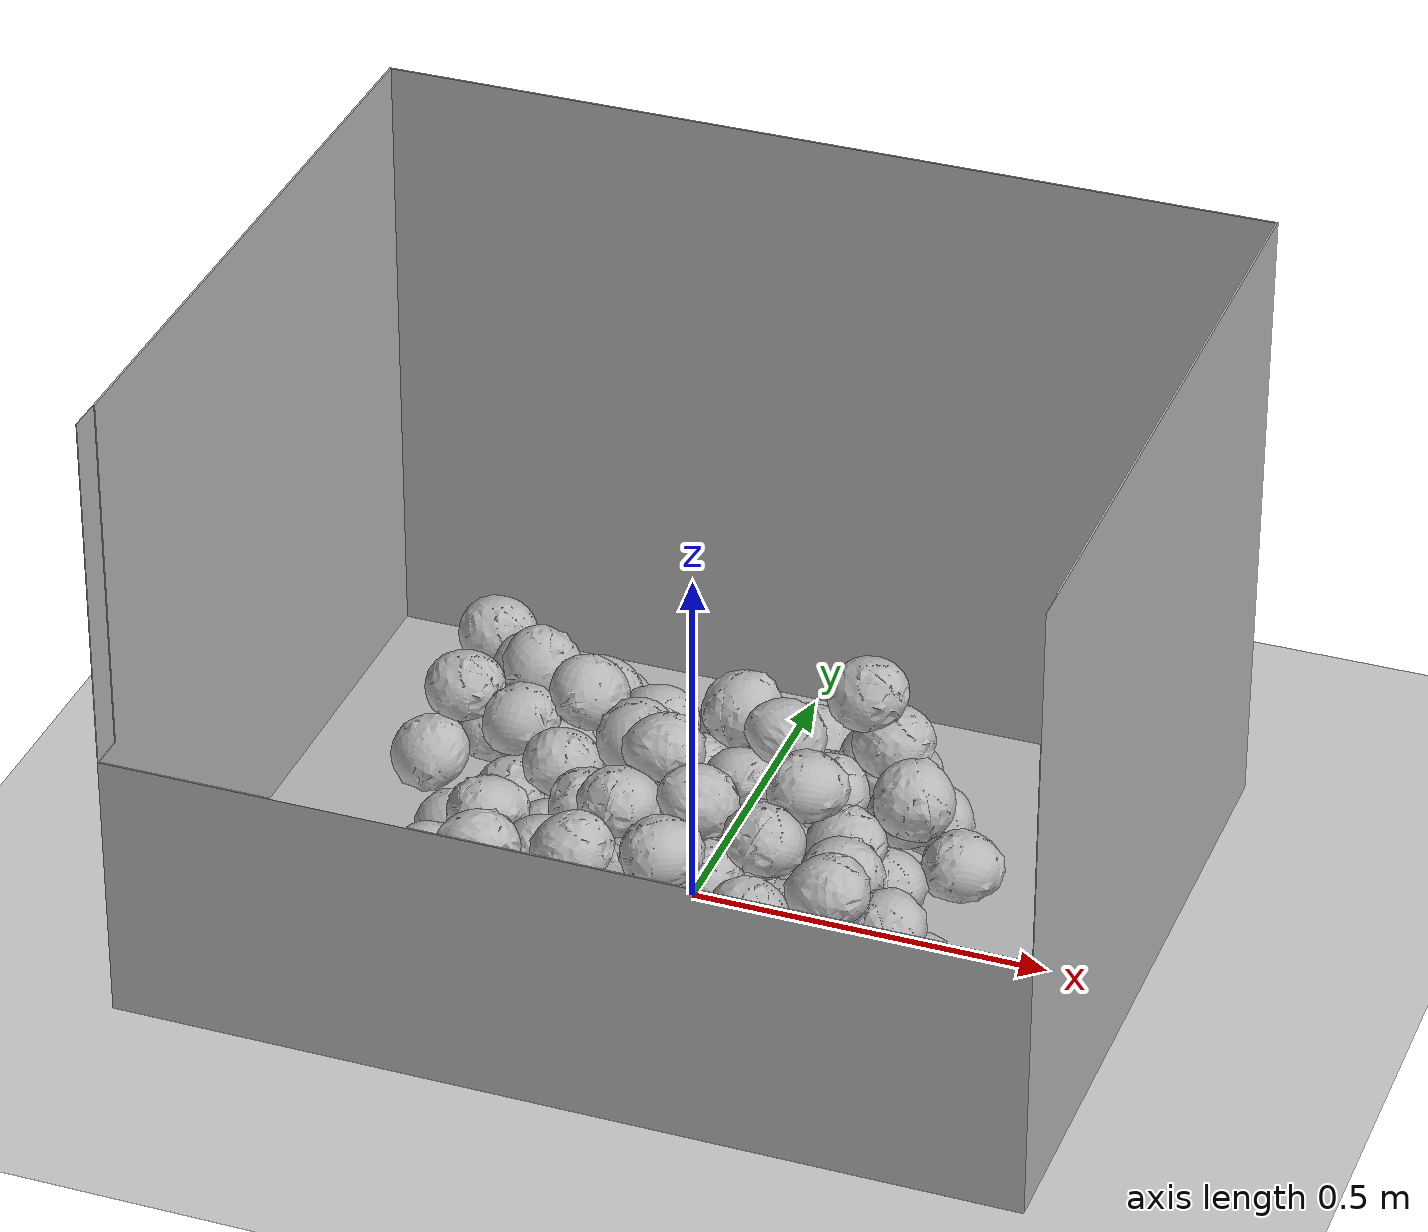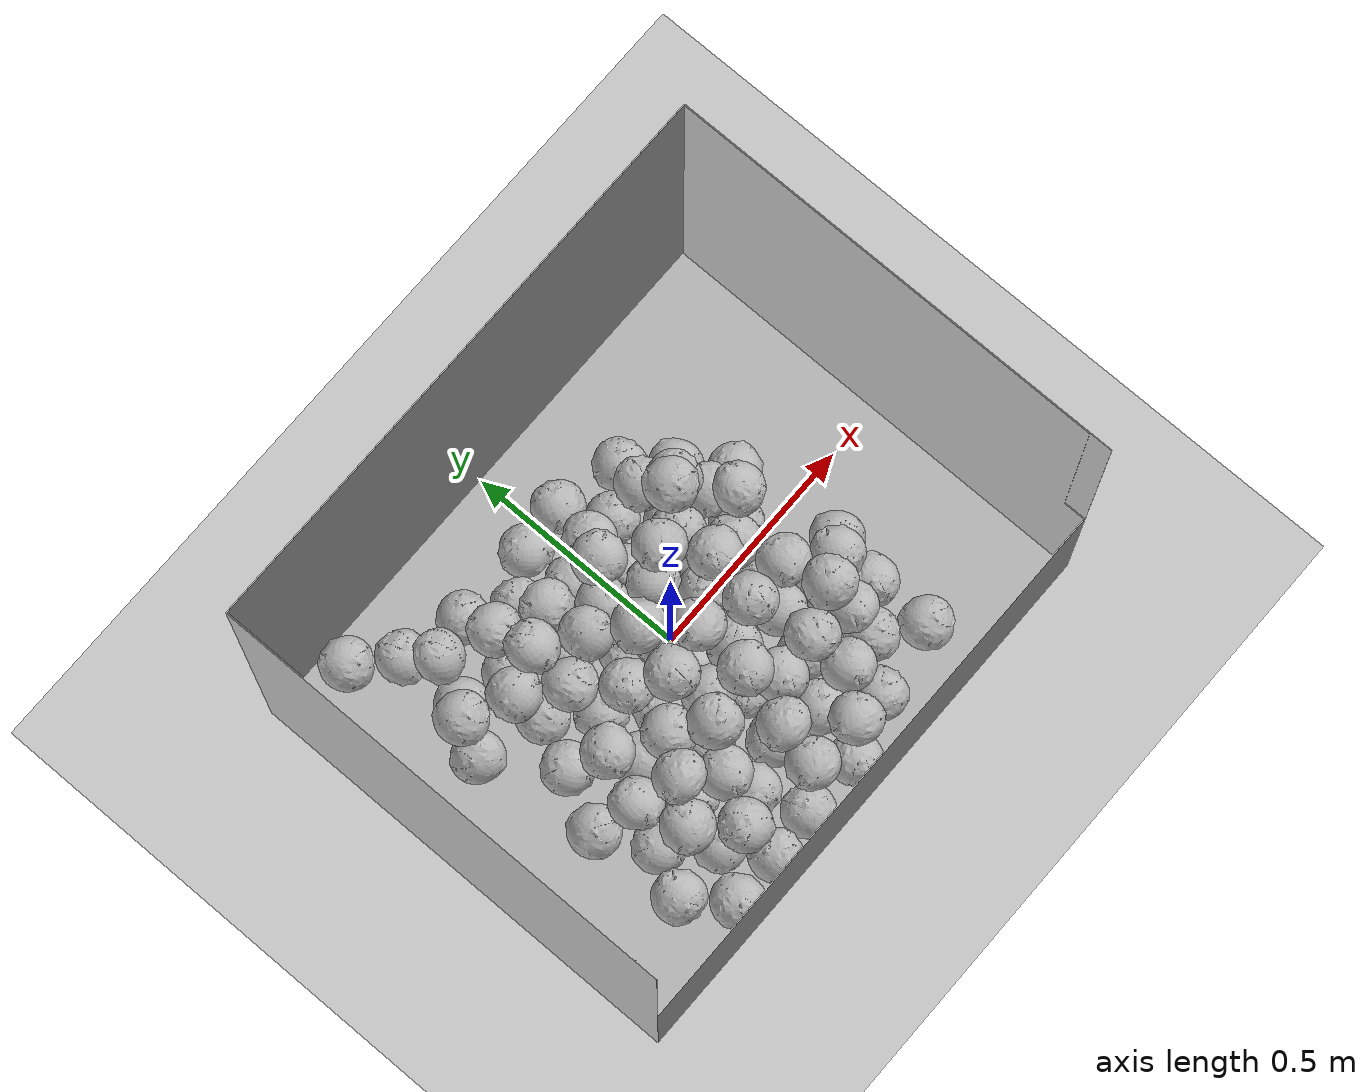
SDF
<sdf version="1.6">
 <world name="default">
  <model name="ground_plane">
   <static>1</static>
   <link name="link">
    <collision name="collision">
     <geometry><plane><normal>0 0 1</normal><size>100 100</size></plane></geometry>
     <surface><friction><ode><mu>100</mu><mu2>50</mu2></ode></friction></surface>
    </collision>
    <visual name="visual">
     <cast_shadows>0</cast_shadows>
     <geometry><plane><normal>0 0 1</normal><size>100 100</size></plane></geometry>
     <material>
      <script><uri>file://media/materials/scripts/gazebo.material</uri><name>Gazebo/Grey</name></script>
     </material>
    </visual>
   </link>
  </model>
  <light name="sun" type="directional">
   <pose>0 0 10 0 -0 0</pose>
   <diffuse>0.8 0.8 0.8 1</diffuse>
   <specular>0.2 0.2 0.2 1</specular>
   <attenuation>
    <range>1000</range>
    <constant>0.9</constant>
    <linear>0.01</linear>
    <quadratic>0.001</quadratic>
   </attenuation>
   <direction>-0.5 0.1 -0.9</direction>
  </light>
  <model name="container">
   <link name="link">
    <inertial>
     <mass>1</mass>
     <inertia><ixx>1</ixx><ixy>0</ixy><ixz>0</ixz><iyy>1</iyy><iyz>0</iyz><izz>1</izz></inertia>
    </inertial>
    <collision name="collision">
     <geometry>
      <mesh>
       <scale>0.001 0.001 0.001</scale>
       <uri>model://big_container_open/big_container_open_meshlab.dae</uri>
      </mesh>
     </geometry>
     <surface>
      <friction><ode><mu>0.6</mu><mu2>0.6</mu2></ode></friction>
      <contact><ode><max_vel>0.1</max_vel><min_depth>0.0001</min_depth></ode></contact>
     </surface>
    </collision>
    <visual name="visual">
     <geometry>
      <mesh>
       <scale>0.001 0.001 0.001</scale>
       <uri>model://big_container_open/big_container_open_meshlab.dae</uri>
      </mesh>
     </geometry>
    </visual>
   </link>
   <pose>4.3e-05 0.001089 -9.3e-05 -2.3e-05 1e-06 -0.000355</pose>
  </model>
  <gravity>0 0 -9.8</gravity>
  <magnetic_field>6e-06 2.3e-05 -4.2e-05</magnetic_field>
  <atmosphere type="adiabatic"/>
  <physics name="default_physics" default="0" type="ode">
   <max_step_size>0.001</max_step_size>
   <real_time_factor>1</real_time_factor>
   <real_time_update_rate>1000</real_time_update_rate>
  </physics>
  <scene><ambient>0.4 0.4 0.4 1</ambient><background>0.7 0.7 0.7 1</background><shadows>1</shadows></scene>
  <audio><device>default</device></audio>
  <spherical_coordinates>
   <surface_model>EARTH_WGS84</surface_model>
   <latitude_deg>0</latitude_deg>
   <longitude_deg>0</longitude_deg>
   <elevation>0</elevation>
   <heading_deg>0</heading_deg>
  </spherical_coordinates>
  <model name="cabbage_0">
   <link name="link">
    <inertial>
     <mass>1</mass>
     <inertia><ixx>0.001</ixx><ixy>0</ixy><ixz>0</ixz><iyy>0.001</iyy><iyz>0</iyz><izz>0.001</izz></inertia>
    </inertial>
    <collision name="collision">
     <geometry>
      <mesh><scale>0.001 0.001 0.001</scale><uri>model://cabbage/cabbage_single.dae</uri></mesh>
     </geometry>
     <surface>
      <friction><ode><mu>0.8</mu><mu2>0.8</mu2></ode></friction>
      <contact><ode><max_vel>0.1</max_vel><min_depth>0.0001</min_depth></ode></contact>
     </surface>
    </collision>
    <visual name="visual">
     <geometry>
      <mesh><scale>0.001 0.001 0.001</scale><uri>model://cabbage/cabbage_single.dae</uri></mesh>
     </geometry>
     <material><script><uri>model://cabbage/texture.material</uri><name>CabbageTexture</name></script></material>
    </visual>
   </link>
   <pose>0.095652 -0.068931 0.004157 1.60014 0.007328 -0.263092</pose>
  </model>
  <model name="cabbage_1">
   <link name="link">
    <inertial>
     <mass>1</mass>
     <inertia><ixx>0.001</ixx><ixy>0</ixy><ixz>0</ixz><iyy>0.001</iyy><iyz>0</iyz><izz>0.001</izz></inertia>
    </inertial>
    <collision name="collision">
     <geometry>
      <mesh><scale>0.001 0.001 0.001</scale><uri>model://cabbage/cabbage_single.dae</uri></mesh>
     </geometry>
     <surface>
      <friction><ode><mu>0.8</mu><mu2>0.8</mu2></ode></friction>
      <contact><ode><max_vel>0.1</max_vel><min_depth>0.0001</min_depth></ode></contact>
     </surface>
    </collision>
    <visual name="visual">
     <geometry>
      <mesh><scale>0.001 0.001 0.001</scale><uri>model://cabbage/cabbage_single.dae</uri></mesh>
     </geometry>
     <material><script><uri>model://cabbage/texture.material</uri><name>CabbageTexture</name></script></material>
    </visual>
   </link>
   <pose>0.338045 0.119369 0.00437 1.61918 0.002361 2.62194</pose>
  </model>
  <model name="cabbage_2">
   <link name="link">
    <inertial>
     <mass>1</mass>
     <inertia><ixx>0.001</ixx><ixy>0</ixy><ixz>0</ixz><iyy>0.001</iyy><iyz>0</iyz><izz>0.001</izz></inertia>
    </inertial>
    <collision name="collision">
     <geometry>
      <mesh><scale>0.001 0.001 0.001</scale><uri>model://cabbage/cabbage_single.dae</uri></mesh>
     </geometry>
     <surface>
      <friction><ode><mu>0.8</mu><mu2>0.8</mu2></ode></friction>
      <contact><ode><max_vel>0.1</max_vel><min_depth>0.0001</min_depth></ode></contact>
     </surface>
    </collision>
    <visual name="visual">
     <geometry>
      <mesh><scale>0.001 0.001 0.001</scale><uri>model://cabbage/cabbage_single.dae</uri></mesh>
     </geometry>
     <material><script><uri>model://cabbage/texture.material</uri><name>CabbageTexture</name></script></material>
    </visual>
   </link>
   <pose>-0.160712 0.134637 0.003951 1.57509 0.007918 -1.36634</pose>
  </model>
  <model name="cabbage_3">
   <link name="link">
    <inertial>
     <mass>1</mass>
     <inertia><ixx>0.001</ixx><ixy>0</ixy><ixz>0</ixz><iyy>0.001</iyy><iyz>0</iyz><izz>0.001</izz></inertia>
    </inertial>
    <collision name="collision">
     <geometry>
      <mesh><scale>0.001 0.001 0.001</scale><uri>model://cabbage/cabbage_single.dae</uri></mesh>
     </geometry>
     <surface>
      <friction><ode><mu>0.8</mu><mu2>0.8</mu2></ode></friction>
      <contact><ode><max_vel>0.1</max_vel><min_depth>0.0001</min_depth></ode></contact>
     </surface>
    </collision>
    <visual name="visual">
     <geometry>
      <mesh><scale>0.001 0.001 0.001</scale><uri>model://cabbage/cabbage_single.dae</uri></mesh>
     </geometry>
     <material><script><uri>model://cabbage/texture.material</uri><name>CabbageTexture</name></script></material>
    </visual>
   </link>
   <pose>0.26333 -0.303335 0.004278 1.61265 0.006299 -1.68663</pose>
  </model>
  <model name="cabbage_4">
   <link name="link">
    <inertial>
     <mass>1</mass>
     <inertia><ixx>0.001</ixx><ixy>0</ixy><ixz>0</ixz><iyy>0.001</iyy><iyz>0</iyz><izz>0.001</izz></inertia>
    </inertial>
    <collision name="collision">
     <geometry>
      <mesh><scale>0.001 0.001 0.001</scale><uri>model://cabbage/cabbage_single.dae</uri></mesh>
     </geometry>
     <surface>
      <friction><ode><mu>0.8</mu><mu2>0.8</mu2></ode></friction>
      <contact><ode><max_vel>0.1</max_vel><min_depth>0.0001</min_depth></ode></contact>
     </surface>
    </collision>
    <visual name="visual">
     <geometry>
      <mesh><scale>0.001 0.001 0.001</scale><uri>model://cabbage/cabbage_single.dae</uri></mesh>
     </geometry>
     <material><script><uri>model://cabbage/texture.material</uri><name>CabbageTexture</name></script></material>
    </visual>
   </link>
   <pose>-0.031392 -0.290349 0.003988 1.57302 0.014128 1.00935</pose>
  </model>
  <model name="cabbage_5">
   <link name="link">
    <inertial>
     <mass>1</mass>
     <inertia><ixx>0.001</ixx><ixy>0</ixy><ixz>0</ixz><iyy>0.001</iyy><iyz>0</iyz><izz>0.001</izz></inertia>
    </inertial>
    <collision name="collision">
     <geometry>
      <mesh><scale>0.001 0.001 0.001</scale><uri>model://cabbage/cabbage_single.dae</uri></mesh>
     </geometry>
     <surface>
      <friction><ode><mu>0.8</mu><mu2>0.8</mu2></ode></friction>
      <contact><ode><max_vel>0.1</max_vel><min_depth>0.0001</min_depth></ode></contact>
     </surface>
    </collision>
    <visual name="visual">
     <geometry>
      <mesh><scale>0.001 0.001 0.001</scale><uri>model://cabbage/cabbage_single.dae</uri></mesh>
     </geometry>
     <material><script><uri>model://cabbage/texture.material</uri><name>CabbageTexture</name></script></material>
    </visual>
   </link>
   <pose>-0.123182 -0.082967 0.005416 1.46042 0.123401 1.52923</pose>
  </model>
  <model name="cabbage_6">
   <link name="link">
    <inertial>
     <mass>1</mass>
     <inertia><ixx>0.001</ixx><ixy>0</ixy><ixz>0</ixz><iyy>0.001</iyy><iyz>0</iyz><izz>0.001</izz></inertia>
    </inertial>
    <collision name="collision">
     <geometry>
      <mesh><scale>0.001 0.001 0.001</scale><uri>model://cabbage/cabbage_single.dae</uri></mesh>
     </geometry>
     <surface>
      <friction><ode><mu>0.8</mu><mu2>0.8</mu2></ode></friction>
      <contact><ode><max_vel>0.1</max_vel><min_depth>0.0001</min_depth></ode></contact>
     </surface>
    </collision>
    <visual name="visual">
     <geometry>
      <mesh><scale>0.001 0.001 0.001</scale><uri>model://cabbage/cabbage_single.dae</uri></mesh>
     </geometry>
     <material><script><uri>model://cabbage/texture.material</uri><name>CabbageTexture</name></script></material>
    </visual>
   </link>
   <pose>0.25772 0.047502 0.004075 1.5633 -0.007798 -2.75672</pose>
  </model>
  <model name="cabbage_7">
   <link name="link">
    <inertial>
     <mass>1</mass>
     <inertia><ixx>0.001</ixx><ixy>0</ixy><ixz>0</ixz><iyy>0.001</iyy><iyz>0</iyz><izz>0.001</izz></inertia>
    </inertial>
    <collision name="collision">
     <geometry>
      <mesh><scale>0.001 0.001 0.001</scale><uri>model://cabbage/cabbage_single.dae</uri></mesh>
     </geometry>
     <surface>
      <friction><ode><mu>0.8</mu><mu2>0.8</mu2></ode></friction>
      <contact><ode><max_vel>0.1</max_vel><min_depth>0.0001</min_depth></ode></contact>
     </surface>
    </collision>
    <visual name="visual">
     <geometry>
      <mesh><scale>0.001 0.001 0.001</scale><uri>model://cabbage/cabbage_single.dae</uri></mesh>
     </geometry>
     <material><script><uri>model://cabbage/texture.material</uri><name>CabbageTexture</name></script></material>
    </visual>
   </link>
   <pose>-0.282449 0.083841 0.005995 1.70223 0.073396 -1.94267</pose>
  </model>
  <model name="cabbage_8">
   <link name="link">
    <inertial>
     <mass>1</mass>
     <inertia><ixx>0.001</ixx><ixy>0</ixy><ixz>0</ixz><iyy>0.001</iyy><iyz>0</iyz><izz>0.001</izz></inertia>
    </inertial>
    <collision name="collision">
     <geometry>
      <mesh><scale>0.001 0.001 0.001</scale><uri>model://cabbage/cabbage_single.dae</uri></mesh>
     </geometry>
     <surface>
      <friction><ode><mu>0.8</mu><mu2>0.8</mu2></ode></friction>
      <contact><ode><max_vel>0.1</max_vel><min_depth>0.0001</min_depth></ode></contact>
     </surface>
    </collision>
    <visual name="visual">
     <geometry>
      <mesh><scale>0.001 0.001 0.001</scale><uri>model://cabbage/cabbage_single.dae</uri></mesh>
     </geometry>
     <material><script><uri>model://cabbage/texture.material</uri><name>CabbageTexture</name></script></material>
    </visual>
   </link>
   <pose>0.144358 -0.227039 0.004095 1.59204 0.007763 2.21992</pose>
  </model>
  <model name="cabbage_9">
   <link name="link">
    <inertial>
     <mass>1</mass>
     <inertia><ixx>0.001</ixx><ixy>0</ixy><ixz>0</ixz><iyy>0.001</iyy><iyz>0</iyz><izz>0.001</izz></inertia>
    </inertial>
    <collision name="collision">
     <geometry>
      <mesh><scale>0.001 0.001 0.001</scale><uri>model://cabbage/cabbage_single.dae</uri></mesh>
     </geometry>
     <surface>
      <friction><ode><mu>0.8</mu><mu2>0.8</mu2></ode></friction>
      <contact><ode><max_vel>0.1</max_vel><min_depth>0.0001</min_depth></ode></contact>
     </surface>
    </collision>
    <visual name="visual">
     <geometry>
      <mesh><scale>0.001 0.001 0.001</scale><uri>model://cabbage/cabbage_single.dae</uri></mesh>
     </geometry>
     <material><script><uri>model://cabbage/texture.material</uri><name>CabbageTexture</name></script></material>
    </visual>
   </link>
   <pose>-0.092201 -0.428561 0.006497 1.65998 -0.10997 0.374089</pose>
  </model>
  <model name="cabbage_10">
   <link name="link">
    <inertial>
     <mass>1</mass>
     <inertia><ixx>0.001</ixx><ixy>0</ixy><ixz>0</ixz><iyy>0.001</iyy><iyz>0</iyz><izz>0.001</izz></inertia>
    </inertial>
    <collision name="collision">
     <geometry>
      <mesh><scale>0.001 0.001 0.001</scale><uri>model://cabbage/cabbage_single.dae</uri></mesh>
     </geometry>
     <surface>
      <friction><ode><mu>0.8</mu><mu2>0.8</mu2></ode></friction>
      <contact><ode><max_vel>0.1</max_vel><min_depth>0.0001</min_depth></ode></contact>
     </surface>
    </collision>
    <visual name="visual">
     <geometry>
      <mesh><scale>0.001 0.001 0.001</scale><uri>model://cabbage/cabbage_single.dae</uri></mesh>
     </geometry>
     <material><script><uri>model://cabbage/texture.material</uri><name>CabbageTexture</name></script></material>
    </visual>
   </link>
   <pose>0.028906 0.041666 0.004637 1.50783 -0.077096 -1.75712</pose>
  </model>
  <model name="cabbage_11">
   <link name="link">
    <inertial>
     <mass>1</mass>
     <inertia><ixx>0.001</ixx><ixy>0</ixy><ixz>0</ixz><iyy>0.001</iyy><iyz>0</iyz><izz>0.001</izz></inertia>
    </inertial>
    <collision name="collision">
     <geometry>
      <mesh><scale>0.001 0.001 0.001</scale><uri>model://cabbage/cabbage_single.dae</uri></mesh>
     </geometry>
     <surface>
      <friction><ode><mu>0.8</mu><mu2>0.8</mu2></ode></friction>
      <contact><ode><max_vel>0.1</max_vel><min_depth>0.0001</min_depth></ode></contact>
     </surface>
    </collision>
    <visual name="visual">
     <geometry>
      <mesh><scale>0.001 0.001 0.001</scale><uri>model://cabbage/cabbage_single.dae</uri></mesh>
     </geometry>
     <material><script><uri>model://cabbage/texture.material</uri><name>CabbageTexture</name></script></material>
    </visual>
   </link>
   <pose>0.178783 0.14303 0.005735 1.46961 -0.171728 -0.377109</pose>
  </model>
  <model name="cabbage_12">
   <link name="link">
    <inertial>
     <mass>1</mass>
     <inertia><ixx>0.001</ixx><ixy>0</ixy><ixz>0</ixz><iyy>0.001</iyy><iyz>0</iyz><izz>0.001</izz></inertia>
    </inertial>
    <collision name="collision">
     <geometry>
      <mesh><scale>0.001 0.001 0.001</scale><uri>model://cabbage/cabbage_single.dae</uri></mesh>
     </geometry>
     <surface>
      <friction><ode><mu>0.8</mu><mu2>0.8</mu2></ode></friction>
      <contact><ode><max_vel>0.1</max_vel><min_depth>0.0001</min_depth></ode></contact>
     </surface>
    </collision>
    <visual name="visual">
     <geometry>
      <mesh><scale>0.001 0.001 0.001</scale><uri>model://cabbage/cabbage_single.dae</uri></mesh>
     </geometry>
     <material><script><uri>model://cabbage/texture.material</uri><name>CabbageTexture</name></script></material>
    </visual>
   </link>
   <pose>-0.238193 0.32125 0.009271 1.46239 -0.340213 -1.06037</pose>
  </model>
  <model name="cabbage_13">
   <link name="link">
    <inertial>
     <mass>1</mass>
     <inertia><ixx>0.001</ixx><ixy>0</ixy><ixz>0</ixz><iyy>0.001</iyy><iyz>0</iyz><izz>0.001</izz></inertia>
    </inertial>
    <collision name="collision">
     <geometry>
      <mesh><scale>0.001 0.001 0.001</scale><uri>model://cabbage/cabbage_single.dae</uri></mesh>
     </geometry>
     <surface>
      <friction><ode><mu>0.8</mu><mu2>0.8</mu2></ode></friction>
      <contact><ode><max_vel>0.1</max_vel><min_depth>0.0001</min_depth></ode></contact>
     </surface>
    </collision>
    <visual name="visual">
     <geometry>
      <mesh><scale>0.001 0.001 0.001</scale><uri>model://cabbage/cabbage_single.dae</uri></mesh>
     </geometry>
     <material><script><uri>model://cabbage/texture.material</uri><name>CabbageTexture</name></script></material>
    </visual>
   </link>
   <pose>0.257826 -0.154445 0.003945 1.57602 0.008658 -0.016472</pose>
  </model>
  <model name="cabbage_14">
   <link name="link">
    <inertial>
     <mass>1</mass>
     <inertia><ixx>0.001</ixx><ixy>0</ixy><ixz>0</ixz><iyy>0.001</iyy><iyz>0</iyz><izz>0.001</izz></inertia>
    </inertial>
    <collision name="collision">
     <geometry>
      <mesh><scale>0.001 0.001 0.001</scale><uri>model://cabbage/cabbage_single.dae</uri></mesh>
     </geometry>
     <surface>
      <friction><ode><mu>0.8</mu><mu2>0.8</mu2></ode></friction>
      <contact><ode><max_vel>0.1</max_vel><min_depth>0.0001</min_depth></ode></contact>
     </surface>
    </collision>
    <visual name="visual">
     <geometry>
      <mesh><scale>0.001 0.001 0.001</scale><uri>model://cabbage/cabbage_single.dae</uri></mesh>
     </geometry>
     <material><script><uri>model://cabbage/texture.material</uri><name>CabbageTexture</name></script></material>
    </visual>
   </link>
   <pose>-0.256394 -0.335493 0.006672 1.7714 -0.058008 0.009481</pose>
  </model>
  <model name="cabbage_15">
   <link name="link">
    <inertial>
     <mass>1</mass>
     <inertia><ixx>0.001</ixx><ixy>0</ixy><ixz>0</ixz><iyy>0.001</iyy><iyz>0</iyz><izz>0.001</izz></inertia>
    </inertial>
    <collision name="collision">
     <geometry>
      <mesh><scale>0.001 0.001 0.001</scale><uri>model://cabbage/cabbage_single.dae</uri></mesh>
     </geometry>
     <surface>
      <friction><ode><mu>0.8</mu><mu2>0.8</mu2></ode></friction>
      <contact><ode><max_vel>0.1</max_vel><min_depth>0.0001</min_depth></ode></contact>
     </surface>
    </collision>
    <visual name="visual">
     <geometry>
      <mesh><scale>0.001 0.001 0.001</scale><uri>model://cabbage/cabbage_single.dae</uri></mesh>
     </geometry>
     <material><script><uri>model://cabbage/texture.material</uri><name>CabbageTexture</name></script></material>
    </visual>
   </link>
   <pose>0.007523 -0.177659 0.005238 1.46223 -0.141863 2.21274</pose>
  </model>
  <model name="cabbage_16">
   <link name="link">
    <inertial>
     <mass>1</mass>
     <inertia><ixx>0.001</ixx><ixy>0</ixy><ixz>0</ixz><iyy>0.001</iyy><iyz>0</iyz><izz>0.001</izz></inertia>
    </inertial>
    <collision name="collision">
     <geometry>
      <mesh><scale>0.001 0.001 0.001</scale><uri>model://cabbage/cabbage_single.dae</uri></mesh>
     </geometry>
     <surface>
      <friction><ode><mu>0.8</mu><mu2>0.8</mu2></ode></friction>
      <contact><ode><max_vel>0.1</max_vel><min_depth>0.0001</min_depth></ode></contact>
     </surface>
    </collision>
    <visual name="visual">
     <geometry>
      <mesh><scale>0.001 0.001 0.001</scale><uri>model://cabbage/cabbage_single.dae</uri></mesh>
     </geometry>
     <material><script><uri>model://cabbage/texture.material</uri><name>CabbageTexture</name></script></material>
    </visual>
   </link>
   <pose>0.198885 0.300354 0.004776 1.49423 -0.095171 -0.896057</pose>
  </model>
  <model name="cabbage_17">
   <link name="link">
    <inertial>
     <mass>1</mass>
     <inertia><ixx>0.001</ixx><ixy>0</ixy><ixz>0</ixz><iyy>0.001</iyy><iyz>0</iyz><izz>0.001</izz></inertia>
    </inertial>
    <collision name="collision">
     <geometry>
      <mesh><scale>0.001 0.001 0.001</scale><uri>model://cabbage/cabbage_single.dae</uri></mesh>
     </geometry>
     <surface>
      <friction><ode><mu>0.8</mu><mu2>0.8</mu2></ode></friction>
      <contact><ode><max_vel>0.1</max_vel><min_depth>0.0001</min_depth></ode></contact>
     </surface>
    </collision>
    <visual name="visual">
     <geometry>
      <mesh><scale>0.001 0.001 0.001</scale><uri>model://cabbage/cabbage_single.dae</uri></mesh>
     </geometry>
     <material><script><uri>model://cabbage/texture.material</uri><name>CabbageTexture</name></script></material>
    </visual>
   </link>
   <pose>-0.206363 0.004883 0.003937 1.57562 0.00821 -1.09915</pose>
  </model>
  <model name="cabbage_18">
   <link name="link">
    <inertial>
     <mass>1</mass>
     <inertia><ixx>0.001</ixx><ixy>0</ixy><ixz>0</ixz><iyy>0.001</iyy><iyz>0</iyz><izz>0.001</izz></inertia>
    </inertial>
    <collision name="collision">
     <geometry>
      <mesh><scale>0.001 0.001 0.001</scale><uri>model://cabbage/cabbage_single.dae</uri></mesh>
     </geometry>
     <surface>
      <friction><ode><mu>0.8</mu><mu2>0.8</mu2></ode></friction>
      <contact><ode><max_vel>0.1</max_vel><min_depth>0.0001</min_depth></ode></contact>
     </surface>
    </collision>
    <visual name="visual">
     <geometry>
      <mesh><scale>0.001 0.001 0.001</scale><uri>model://cabbage/cabbage_single.dae</uri></mesh>
     </geometry>
     <material><script><uri>model://cabbage/texture.material</uri><name>CabbageTexture</name></script></material>
    </visual>
   </link>
   <pose>0.177823 -0.389709 0.00418 1.55977 0.036699 -0.992467</pose>
  </model>
  <model name="cabbage_19">
   <link name="link">
    <inertial>
     <mass>1</mass>
     <inertia><ixx>0.001</ixx><ixy>0</ixy><ixz>0</ixz><iyy>0.001</iyy><iyz>0</iyz><izz>0.001</izz></inertia>
    </inertial>
    <collision name="collision">
     <geometry>
      <mesh><scale>0.001 0.001 0.001</scale><uri>model://cabbage/cabbage_single.dae</uri></mesh>
     </geometry>
     <surface>
      <friction><ode><mu>0.8</mu><mu2>0.8</mu2></ode></friction>
      <contact><ode><max_vel>0.1</max_vel><min_depth>0.0001</min_depth></ode></contact>
     </surface>
    </collision>
    <visual name="visual">
     <geometry>
      <mesh><scale>0.001 0.001 0.001</scale><uri>model://cabbage/cabbage_single.dae</uri></mesh>
     </geometry>
     <material><script><uri>model://cabbage/texture.material</uri><name>CabbageTexture</name></script></material>
    </visual>
   </link>
   <pose>-0.223103 -0.118078 0.006149 1.41108 -0.183366 0.392662</pose>
  </model>
  <model name="cabbage_20">
   <link name="link">
    <inertial>
     <mass>1</mass>
     <inertia><ixx>0.001</ixx><ixy>0</ixy><ixz>0</ixz><iyy>0.001</iyy><iyz>0</iyz><izz>0.001</izz></inertia>
    </inertial>
    <collision name="collision">
     <geometry>
      <mesh><scale>0.001 0.001 0.001</scale><uri>model://cabbage/cabbage_single.dae</uri></mesh>
     </geometry>
     <surface>
      <friction><ode><mu>0.8</mu><mu2>0.8</mu2></ode></friction>
      <contact><ode><max_vel>0.1</max_vel><min_depth>0.0001</min_depth></ode></contact>
     </surface>
    </collision>
    <visual name="visual">
     <geometry>
      <mesh><scale>0.001 0.001 0.001</scale><uri>model://cabbage/cabbage_single.dae</uri></mesh>
     </geometry>
     <material><script><uri>model://cabbage/texture.material</uri><name>CabbageTexture</name></script></material>
    </visual>
   </link>
   <pose>0.141362 0.032322 0.004782 1.49274 -0.096805 -1.60788</pose>
  </model>
  <model name="cabbage_21">
   <link name="link">
    <inertial>
     <mass>1</mass>
     <inertia><ixx>0.001</ixx><ixy>0</ixy><ixz>0</ixz><iyy>0.001</iyy><iyz>0</iyz><izz>0.001</izz></inertia>
    </inertial>
    <collision name="collision">
     <geometry>
      <mesh><scale>0.001 0.001 0.001</scale><uri>model://cabbage/cabbage_single.dae</uri></mesh>
     </geometry>
     <surface>
      <friction><ode><mu>0.8</mu><mu2>0.8</mu2></ode></friction>
      <contact><ode><max_vel>0.1</max_vel><min_depth>0.0001</min_depth></ode></contact>
     </surface>
    </collision>
    <visual name="visual">
     <geometry>
      <mesh><scale>0.001 0.001 0.001</scale><uri>model://cabbage/cabbage_single.dae</uri></mesh>
     </geometry>
     <material><script><uri>model://cabbage/texture.material</uri><name>CabbageTexture</name></script></material>
    </visual>
   </link>
   <pose>0.265352 0.217555 0.004623 1.50916 -0.07587 -2.79041</pose>
  </model>
  <model name="cabbage_22">
   <link name="link">
    <inertial>
     <mass>1</mass>
     <inertia><ixx>0.001</ixx><ixy>0</ixy><ixz>0</ixz><iyy>0.001</iyy><iyz>0</iyz><izz>0.001</izz></inertia>
    </inertial>
    <collision name="collision">
     <geometry>
      <mesh><scale>0.001 0.001 0.001</scale><uri>model://cabbage/cabbage_single.dae</uri></mesh>
     </geometry>
     <surface>
      <friction><ode><mu>0.8</mu><mu2>0.8</mu2></ode></friction>
      <contact><ode><max_vel>0.1</max_vel><min_depth>0.0001</min_depth></ode></contact>
     </surface>
    </collision>
    <visual name="visual">
     <geometry>
      <mesh><scale>0.001 0.001 0.001</scale><uri>model://cabbage/cabbage_single.dae</uri></mesh>
     </geometry>
     <material><script><uri>model://cabbage/texture.material</uri><name>CabbageTexture</name></script></material>
    </visual>
   </link>
   <pose>-0.046239 0.211124 0.006612 1.37012 0.133765 1.20828</pose>
  </model>
  <model name="cabbage_23">
   <link name="link">
    <inertial>
     <mass>1</mass>
     <inertia><ixx>0.001</ixx><ixy>0</ixy><ixz>0</ixz><iyy>0.001</iyy><iyz>0</iyz><izz>0.001</izz></inertia>
    </inertial>
    <collision name="collision">
     <geometry>
      <mesh><scale>0.001 0.001 0.001</scale><uri>model://cabbage/cabbage_single.dae</uri></mesh>
     </geometry>
     <surface>
      <friction><ode><mu>0.8</mu><mu2>0.8</mu2></ode></friction>
      <contact><ode><max_vel>0.1</max_vel><min_depth>0.0001</min_depth></ode></contact>
     </surface>
    </collision>
    <visual name="visual">
     <geometry>
      <mesh><scale>0.001 0.001 0.001</scale><uri>model://cabbage/cabbage_single.dae</uri></mesh>
     </geometry>
     <material><script><uri>model://cabbage/texture.material</uri><name>CabbageTexture</name></script></material>
    </visual>
   </link>
   <pose>0.342589 -0.232944 0.003949 1.57656 0.007596 2.96856</pose>
  </model>
  <model name="cabbage_24">
   <link name="link">
    <inertial>
     <mass>1</mass>
     <inertia><ixx>0.001</ixx><ixy>0</ixy><ixz>0</ixz><iyy>0.001</iyy><iyz>0</iyz><izz>0.001</izz></inertia>
    </inertial>
    <collision name="collision">
     <geometry>
      <mesh><scale>0.001 0.001 0.001</scale><uri>model://cabbage/cabbage_single.dae</uri></mesh>
     </geometry>
     <surface>
      <friction><ode><mu>0.8</mu><mu2>0.8</mu2></ode></friction>
      <contact><ode><max_vel>0.1</max_vel><min_depth>0.0001</min_depth></ode></contact>
     </surface>
    </collision>
    <visual name="visual">
     <geometry>
      <mesh><scale>0.001 0.001 0.001</scale><uri>model://cabbage/cabbage_single.dae</uri></mesh>
     </geometry>
     <material><script><uri>model://cabbage/texture.material</uri><name>CabbageTexture</name></script></material>
    </visual>
   </link>
   <pose>-0.117569 -0.195493 0.003917 1.57591 0.008334 2.5017</pose>
  </model>
  <model name="cabbage_25">
   <link name="link">
    <inertial>
     <mass>1</mass>
     <inertia><ixx>0.001</ixx><ixy>0</ixy><ixz>0</ixz><iyy>0.001</iyy><iyz>0</iyz><izz>0.001</izz></inertia>
    </inertial>
    <collision name="collision">
     <geometry>
      <mesh><scale>0.001 0.001 0.001</scale><uri>model://cabbage/cabbage_single.dae</uri></mesh>
     </geometry>
     <surface>
      <friction><ode><mu>0.8</mu><mu2>0.8</mu2></ode></friction>
      <contact><ode><max_vel>0.1</max_vel><min_depth>0.0001</min_depth></ode></contact>
     </surface>
    </collision>
    <visual name="visual">
     <geometry>
      <mesh><scale>0.001 0.001 0.001</scale><uri>model://cabbage/cabbage_single.dae</uri></mesh>
     </geometry>
     <material><script><uri>model://cabbage/texture.material</uri><name>CabbageTexture</name></script></material>
    </visual>
   </link>
   <pose>-0.028365 -0.073903 0.009732 1.2463 -0.214871 -1.57877</pose>
  </model>
  <model name="cabbage_26">
   <link name="link">
    <inertial>
     <mass>1</mass>
     <inertia><ixx>0.001</ixx><ixy>0</ixy><ixz>0</ixz><iyy>0.001</iyy><iyz>0</iyz><izz>0.001</izz></inertia>
    </inertial>
    <collision name="collision">
     <geometry>
      <mesh><scale>0.001 0.001 0.001</scale><uri>model://cabbage/cabbage_single.dae</uri></mesh>
     </geometry>
     <surface>
      <friction><ode><mu>0.8</mu><mu2>0.8</mu2></ode></friction>
      <contact><ode><max_vel>0.1</max_vel><min_depth>0.0001</min_depth></ode></contact>
     </surface>
    </collision>
    <visual name="visual">
     <geometry>
      <mesh><scale>0.001 0.001 0.001</scale><uri>model://cabbage/cabbage_single.dae</uri></mesh>
     </geometry>
     <material><script><uri>model://cabbage/texture.material</uri><name>CabbageTexture</name></script></material>
    </visual>
   </link>
   <pose>0.103957 0.234161 0.005956 1.4439 -0.20006 -1.04395</pose>
  </model>
  <model name="cabbage_27">
   <link name="link">
    <inertial>
     <mass>1</mass>
     <inertia><ixx>0.001</ixx><ixy>0</ixy><ixz>0</ixz><iyy>0.001</iyy><iyz>0</iyz><izz>0.001</izz></inertia>
    </inertial>
    <collision name="collision">
     <geometry>
      <mesh><scale>0.001 0.001 0.001</scale><uri>model://cabbage/cabbage_single.dae</uri></mesh>
     </geometry>
     <surface>
      <friction><ode><mu>0.8</mu><mu2>0.8</mu2></ode></friction>
      <contact><ode><max_vel>0.1</max_vel><min_depth>0.0001</min_depth></ode></contact>
     </surface>
    </collision>
    <visual name="visual">
     <geometry>
      <mesh><scale>0.001 0.001 0.001</scale><uri>model://cabbage/cabbage_single.dae</uri></mesh>
     </geometry>
     <material><script><uri>model://cabbage/texture.material</uri><name>CabbageTexture</name></script></material>
    </visual>
   </link>
   <pose>-0.336447 -0.021497 0.004791 1.50554 0.032377 1.19338</pose>
  </model>
  <model name="cabbage_28">
   <link name="link">
    <inertial>
     <mass>1</mass>
     <inertia><ixx>0.001</ixx><ixy>0</ixy><ixz>0</ixz><iyy>0.001</iyy><iyz>0</iyz><izz>0.001</izz></inertia>
    </inertial>
    <collision name="collision">
     <geometry>
      <mesh><scale>0.001 0.001 0.001</scale><uri>model://cabbage/cabbage_single.dae</uri></mesh>
     </geometry>
     <surface>
      <friction><ode><mu>0.8</mu><mu2>0.8</mu2></ode></friction>
      <contact><ode><max_vel>0.1</max_vel><min_depth>0.0001</min_depth></ode></contact>
     </surface>
    </collision>
    <visual name="visual">
     <geometry>
      <mesh><scale>0.001 0.001 0.001</scale><uri>model://cabbage/cabbage_single.dae</uri></mesh>
     </geometry>
     <material><script><uri>model://cabbage/texture.material</uri><name>CabbageTexture</name></script></material>
    </visual>
   </link>
   <pose>0.213279 -0.04941 0.004406 1.5299 -0.049896 1.51269</pose>
  </model>
  <model name="cabbage_29">
   <link name="link">
    <inertial>
     <mass>1</mass>
     <inertia><ixx>0.001</ixx><ixy>0</ixy><ixz>0</ixz><iyy>0.001</iyy><iyz>0</iyz><izz>0.001</izz></inertia>
    </inertial>
    <collision name="collision">
     <geometry>
      <mesh><scale>0.001 0.001 0.001</scale><uri>model://cabbage/cabbage_single.dae</uri></mesh>
     </geometry>
     <surface>
      <friction><ode><mu>0.8</mu><mu2>0.8</mu2></ode></friction>
      <contact><ode><max_vel>0.1</max_vel><min_depth>0.0001</min_depth></ode></contact>
     </surface>
    </collision>
    <visual name="visual">
     <geometry>
      <mesh><scale>0.001 0.001 0.001</scale><uri>model://cabbage/cabbage_single.dae</uri></mesh>
     </geometry>
     <material><script><uri>model://cabbage/texture.material</uri><name>CabbageTexture</name></script></material>
    </visual>
   </link>
   <pose>-0.336674 -0.259183 0.005064 1.47229 0.012889 1.13985</pose>
  </model>
  <model name="cabbage_30">
   <link name="link">
    <inertial>
     <mass>1</mass>
     <inertia><ixx>0.001</ixx><ixy>0</ixy><ixz>0</ixz><iyy>0.001</iyy><iyz>0</iyz><izz>0.001</izz></inertia>
    </inertial>
    <collision name="collision">
     <geometry>
      <mesh><scale>0.001 0.001 0.001</scale><uri>model://cabbage/cabbage_single.dae</uri></mesh>
     </geometry>
     <surface>
      <friction><ode><mu>0.8</mu><mu2>0.8</mu2></ode></friction>
      <contact><ode><max_vel>0.1</max_vel><min_depth>0.0001</min_depth></ode></contact>
     </surface>
    </collision>
    <visual name="visual">
     <geometry>
      <mesh><scale>0.001 0.001 0.001</scale><uri>model://cabbage/cabbage_single.dae</uri></mesh>
     </geometry>
     <material><script><uri>model://cabbage/texture.material</uri><name>CabbageTexture</name></script></material>
    </visual>
   </link>
   <pose>0.033468 0.131767 0.014044 2.02488 0.188294 2.44404</pose>
  </model>
  <model name="cabbage_31">
   <link name="link">
    <inertial>
     <mass>1</mass>
     <inertia><ixx>0.001</ixx><ixy>0</ixy><ixz>0</ixz><iyy>0.001</iyy><iyz>0</iyz><izz>0.001</izz></inertia>
    </inertial>
    <collision name="collision">
     <geometry>
      <mesh><scale>0.001 0.001 0.001</scale><uri>model://cabbage/cabbage_single.dae</uri></mesh>
     </geometry>
     <surface>
      <friction><ode><mu>0.8</mu><mu2>0.8</mu2></ode></friction>
      <contact><ode><max_vel>0.1</max_vel><min_depth>0.0001</min_depth></ode></contact>
     </surface>
    </collision>
    <visual name="visual">
     <geometry>
      <mesh><scale>0.001 0.001 0.001</scale><uri>model://cabbage/cabbage_single.dae</uri></mesh>
     </geometry>
     <material><script><uri>model://cabbage/texture.material</uri><name>CabbageTexture</name></script></material>
    </visual>
   </link>
   <pose>0.26403 0.126406 0.067112 1.43911 -0.097355 0.175454</pose>
  </model>
  <model name="cabbage_32">
   <link name="link">
    <inertial>
     <mass>1</mass>
     <inertia><ixx>0.001</ixx><ixy>0</ixy><ixz>0</ixz><iyy>0.001</iyy><iyz>0</iyz><izz>0.001</izz></inertia>
    </inertial>
    <collision name="collision">
     <geometry>
      <mesh><scale>0.001 0.001 0.001</scale><uri>model://cabbage/cabbage_single.dae</uri></mesh>
     </geometry>
     <surface>
      <friction><ode><mu>0.8</mu><mu2>0.8</mu2></ode></friction>
      <contact><ode><max_vel>0.1</max_vel><min_depth>0.0001</min_depth></ode></contact>
     </surface>
    </collision>
    <visual name="visual">
     <geometry>
      <mesh><scale>0.001 0.001 0.001</scale><uri>model://cabbage/cabbage_single.dae</uri></mesh>
     </geometry>
     <material><script><uri>model://cabbage/texture.material</uri><name>CabbageTexture</name></script></material>
    </visual>
   </link>
   <pose>-0.376612 0.220758 0.004318 1.53156 -0.047835 -2.41315</pose>
  </model>
  <model name="cabbage_33">
   <link name="link">
    <inertial>
     <mass>1</mass>
     <inertia><ixx>0.001</ixx><ixy>0</ixy><ixz>0</ixz><iyy>0.001</iyy><iyz>0</iyz><izz>0.001</izz></inertia>
    </inertial>
    <collision name="collision">
     <geometry>
      <mesh><scale>0.001 0.001 0.001</scale><uri>model://cabbage/cabbage_single.dae</uri></mesh>
     </geometry>
     <surface>
      <friction><ode><mu>0.8</mu><mu2>0.8</mu2></ode></friction>
      <contact><ode><max_vel>0.1</max_vel><min_depth>0.0001</min_depth></ode></contact>
     </surface>
    </collision>
    <visual name="visual">
     <geometry>
      <mesh><scale>0.001 0.001 0.001</scale><uri>model://cabbage/cabbage_single.dae</uri></mesh>
     </geometry>
     <material><script><uri>model://cabbage/texture.material</uri><name>CabbageTexture</name></script></material>
    </visual>
   </link>
   <pose>0.176023 -0.136395 0.05431 1.38701 -0.008547 1.23999</pose>
  </model>
  <model name="cabbage_34">
   <link name="link">
    <inertial>
     <mass>1</mass>
     <inertia><ixx>0.001</ixx><ixy>0</ixy><ixz>0</ixz><iyy>0.001</iyy><iyz>0</iyz><izz>0.001</izz></inertia>
    </inertial>
    <collision name="collision">
     <geometry>
      <mesh><scale>0.001 0.001 0.001</scale><uri>model://cabbage/cabbage_single.dae</uri></mesh>
     </geometry>
     <surface>
      <friction><ode><mu>0.8</mu><mu2>0.8</mu2></ode></friction>
      <contact><ode><max_vel>0.1</max_vel><min_depth>0.0001</min_depth></ode></contact>
     </surface>
    </collision>
    <visual name="visual">
     <geometry>
      <mesh><scale>0.001 0.001 0.001</scale><uri>model://cabbage/cabbage_single.dae</uri></mesh>
     </geometry>
     <material><script><uri>model://cabbage/texture.material</uri><name>CabbageTexture</name></script></material>
    </visual>
   </link>
   <pose>-0.382624 -0.145849 0.009496 1.88399 0.106803 -2.03489</pose>
  </model>
  <model name="cabbage_35">
   <link name="link">
    <inertial>
     <mass>1</mass>
     <inertia><ixx>0.001</ixx><ixy>0</ixy><ixz>0</ixz><iyy>0.001</iyy><iyz>0</iyz><izz>0.001</izz></inertia>
    </inertial>
    <collision name="collision">
     <geometry>
      <mesh><scale>0.001 0.001 0.001</scale><uri>model://cabbage/cabbage_single.dae</uri></mesh>
     </geometry>
     <surface>
      <friction><ode><mu>0.8</mu><mu2>0.8</mu2></ode></friction>
      <contact><ode><max_vel>0.1</max_vel><min_depth>0.0001</min_depth></ode></contact>
     </surface>
    </collision>
    <visual name="visual">
     <geometry>
      <mesh><scale>0.001 0.001 0.001</scale><uri>model://cabbage/cabbage_single.dae</uri></mesh>
     </geometry>
     <material><script><uri>model://cabbage/texture.material</uri><name>CabbageTexture</name></script></material>
    </visual>
   </link>
   <pose>0.11408 -0.007497 0.08358 1.91992 -0.289045 -1.10072</pose>
  </model>
  <model name="cabbage_36">
   <link name="link">
    <inertial>
     <mass>1</mass>
     <inertia><ixx>0.001</ixx><ixy>0</ixy><ixz>0</ixz><iyy>0.001</iyy><iyz>0</iyz><izz>0.001</izz></inertia>
    </inertial>
    <collision name="collision">
     <geometry>
      <mesh><scale>0.001 0.001 0.001</scale><uri>model://cabbage/cabbage_single.dae</uri></mesh>
     </geometry>
     <surface>
      <friction><ode><mu>0.8</mu><mu2>0.8</mu2></ode></friction>
      <contact><ode><max_vel>0.1</max_vel><min_depth>0.0001</min_depth></ode></contact>
     </surface>
    </collision>
    <visual name="visual">
     <geometry>
      <mesh><scale>0.001 0.001 0.001</scale><uri>model://cabbage/cabbage_single.dae</uri></mesh>
     </geometry>
     <material><script><uri>model://cabbage/texture.material</uri><name>CabbageTexture</name></script></material>
    </visual>
   </link>
   <pose>0.178663 0.255461 0.076212 1.98723 0.223029 -0.199707</pose>
  </model>
  <model name="cabbage_37">
   <link name="link">
    <inertial>
     <mass>1</mass>
     <inertia><ixx>0.001</ixx><ixy>0</ixy><ixz>0</ixz><iyy>0.001</iyy><iyz>0</iyz><izz>0.001</izz></inertia>
    </inertial>
    <collision name="collision">
     <geometry>
      <mesh><scale>0.001 0.001 0.001</scale><uri>model://cabbage/cabbage_single.dae</uri></mesh>
     </geometry>
     <surface>
      <friction><ode><mu>0.8</mu><mu2>0.8</mu2></ode></friction>
      <contact><ode><max_vel>0.1</max_vel><min_depth>0.0001</min_depth></ode></contact>
     </surface>
    </collision>
    <visual name="visual">
     <geometry>
      <mesh><scale>0.001 0.001 0.001</scale><uri>model://cabbage/cabbage_single.dae</uri></mesh>
     </geometry>
     <material><script><uri>model://cabbage/texture.material</uri><name>CabbageTexture</name></script></material>
    </visual>
   </link>
   <pose>-0.423853 0.14604 0.012931 1.47782 -0.495156 1.10701</pose>
  </model>
  <model name="cabbage_38">
   <link name="link">
    <inertial>
     <mass>1</mass>
     <inertia><ixx>0.001</ixx><ixy>0</ixy><ixz>0</ixz><iyy>0.001</iyy><iyz>0</iyz><izz>0.001</izz></inertia>
    </inertial>
    <collision name="collision">
     <geometry>
      <mesh><scale>0.001 0.001 0.001</scale><uri>model://cabbage/cabbage_single.dae</uri></mesh>
     </geometry>
     <surface>
      <friction><ode><mu>0.8</mu><mu2>0.8</mu2></ode></friction>
      <contact><ode><max_vel>0.1</max_vel><min_depth>0.0001</min_depth></ode></contact>
     </surface>
    </collision>
    <visual name="visual">
     <geometry>
      <mesh><scale>0.001 0.001 0.001</scale><uri>model://cabbage/cabbage_single.dae</uri></mesh>
     </geometry>
     <material><script><uri>model://cabbage/texture.material</uri><name>CabbageTexture</name></script></material>
    </visual>
   </link>
   <pose>0.041406 -0.434485 0.005413 1.44281 -0.136354 2.85036</pose>
  </model>
  <model name="cabbage_39">
   <link name="link">
    <inertial>
     <mass>1</mass>
     <inertia><ixx>0.001</ixx><ixy>0</ixy><ixz>0</ixz><iyy>0.001</iyy><iyz>0</iyz><izz>0.001</izz></inertia>
    </inertial>
    <collision name="collision">
     <geometry>
      <mesh><scale>0.001 0.001 0.001</scale><uri>model://cabbage/cabbage_single.dae</uri></mesh>
     </geometry>
     <surface>
      <friction><ode><mu>0.8</mu><mu2>0.8</mu2></ode></friction>
      <contact><ode><max_vel>0.1</max_vel><min_depth>0.0001</min_depth></ode></contact>
     </surface>
    </collision>
    <visual name="visual">
     <geometry>
      <mesh><scale>0.001 0.001 0.001</scale><uri>model://cabbage/cabbage_single.dae</uri></mesh>
     </geometry>
     <material><script><uri>model://cabbage/texture.material</uri><name>CabbageTexture</name></script></material>
    </visual>
   </link>
   <pose>-0.119221 -0.321247 0.009598 1.53789 0.350993 -2.77977</pose>
  </model>
  <model name="cabbage_40">
   <link name="link">
    <inertial>
     <mass>1</mass>
     <inertia><ixx>0.001</ixx><ixy>0</ixy><ixz>0</ixz><iyy>0.001</iyy><iyz>0</iyz><izz>0.001</izz></inertia>
    </inertial>
    <collision name="collision">
     <geometry>
      <mesh><scale>0.001 0.001 0.001</scale><uri>model://cabbage/cabbage_single.dae</uri></mesh>
     </geometry>
     <surface>
      <friction><ode><mu>0.8</mu><mu2>0.8</mu2></ode></friction>
      <contact><ode><max_vel>0.1</max_vel><min_depth>0.0001</min_depth></ode></contact>
     </surface>
    </collision>
    <visual name="visual">
     <geometry>
      <mesh><scale>0.001 0.001 0.001</scale><uri>model://cabbage/cabbage_single.dae</uri></mesh>
     </geometry>
     <material><script><uri>model://cabbage/texture.material</uri><name>CabbageTexture</name></script></material>
    </visual>
   </link>
   <pose>-0.085167 0.05034 0.003951 1.57538 0.009382 1.75053</pose>
  </model>
  <model name="cabbage_41">
   <link name="link">
    <inertial>
     <mass>1</mass>
     <inertia><ixx>0.001</ixx><ixy>0</ixy><ixz>0</ixz><iyy>0.001</iyy><iyz>0</iyz><izz>0.001</izz></inertia>
    </inertial>
    <collision name="collision">
     <geometry>
      <mesh><scale>0.001 0.001 0.001</scale><uri>model://cabbage/cabbage_single.dae</uri></mesh>
     </geometry>
     <surface>
      <friction><ode><mu>0.8</mu><mu2>0.8</mu2></ode></friction>
      <contact><ode><max_vel>0.1</max_vel><min_depth>0.0001</min_depth></ode></contact>
     </surface>
    </collision>
    <visual name="visual">
     <geometry>
      <mesh><scale>0.001 0.001 0.001</scale><uri>model://cabbage/cabbage_single.dae</uri></mesh>
     </geometry>
     <material><script><uri>model://cabbage/texture.material</uri><name>CabbageTexture</name></script></material>
    </visual>
   </link>
   <pose>0.219704 0.025738 0.081941 1.76958 -0.164206 -0.279248</pose>
  </model>
  <model name="cabbage_42">
   <link name="link">
    <inertial>
     <mass>1</mass>
     <inertia><ixx>0.001</ixx><ixy>0</ixy><ixz>0</ixz><iyy>0.001</iyy><iyz>0</iyz><izz>0.001</izz></inertia>
    </inertial>
    <collision name="collision">
     <geometry>
      <mesh><scale>0.001 0.001 0.001</scale><uri>model://cabbage/cabbage_single.dae</uri></mesh>
     </geometry>
     <surface>
      <friction><ode><mu>0.8</mu><mu2>0.8</mu2></ode></friction>
      <contact><ode><max_vel>0.1</max_vel><min_depth>0.0001</min_depth></ode></contact>
     </surface>
    </collision>
    <visual name="visual">
     <geometry>
      <mesh><scale>0.001 0.001 0.001</scale><uri>model://cabbage/cabbage_single.dae</uri></mesh>
     </geometry>
     <material><script><uri>model://cabbage/texture.material</uri><name>CabbageTexture</name></script></material>
    </visual>
   </link>
   <pose>-0.221262 0.067492 0.074463 1.46171 -0.194613 -1.89476</pose>
  </model>
  <model name="cabbage_43">
   <link name="link">
    <inertial>
     <mass>1</mass>
     <inertia><ixx>0.001</ixx><ixy>0</ixy><ixz>0</ixz><iyy>0.001</iyy><iyz>0</iyz><izz>0.001</izz></inertia>
    </inertial>
    <collision name="collision">
     <geometry>
      <mesh><scale>0.001 0.001 0.001</scale><uri>model://cabbage/cabbage_single.dae</uri></mesh>
     </geometry>
     <surface>
      <friction><ode><mu>0.8</mu><mu2>0.8</mu2></ode></friction>
      <contact><ode><max_vel>0.1</max_vel><min_depth>0.0001</min_depth></ode></contact>
     </surface>
    </collision>
    <visual name="visual">
     <geometry>
      <mesh><scale>0.001 0.001 0.001</scale><uri>model://cabbage/cabbage_single.dae</uri></mesh>
     </geometry>
     <material><script><uri>model://cabbage/texture.material</uri><name>CabbageTexture</name></script></material>
    </visual>
   </link>
   <pose>-0.031149 -0.397083 0.063675 1.22152 0.056045 -0.294026</pose>
  </model>
  <model name="cabbage_44">
   <link name="link">
    <inertial>
     <mass>1</mass>
     <inertia><ixx>0.001</ixx><ixy>0</ixy><ixz>0</ixz><iyy>0.001</iyy><iyz>0</iyz><izz>0.001</izz></inertia>
    </inertial>
    <collision name="collision">
     <geometry>
      <mesh><scale>0.001 0.001 0.001</scale><uri>model://cabbage/cabbage_single.dae</uri></mesh>
     </geometry>
     <surface>
      <friction><ode><mu>0.8</mu><mu2>0.8</mu2></ode></friction>
      <contact><ode><max_vel>0.1</max_vel><min_depth>0.0001</min_depth></ode></contact>
     </surface>
    </collision>
    <visual name="visual">
     <geometry>
      <mesh><scale>0.001 0.001 0.001</scale><uri>model://cabbage/cabbage_single.dae</uri></mesh>
     </geometry>
     <material><script><uri>model://cabbage/texture.material</uri><name>CabbageTexture</name></script></material>
    </visual>
   </link>
   <pose>-0.231266 -0.253244 0.008444 1.53178 0.305616 1.14866</pose>
  </model>
  <model name="cabbage_45">
   <link name="link">
    <inertial>
     <mass>1</mass>
     <inertia><ixx>0.001</ixx><ixy>0</ixy><ixz>0</ixz><iyy>0.001</iyy><iyz>0</iyz><izz>0.001</izz></inertia>
    </inertial>
    <collision name="collision">
     <geometry>
      <mesh><scale>0.001 0.001 0.001</scale><uri>model://cabbage/cabbage_single.dae</uri></mesh>
     </geometry>
     <surface>
      <friction><ode><mu>0.8</mu><mu2>0.8</mu2></ode></friction>
      <contact><ode><max_vel>0.1</max_vel><min_depth>0.0001</min_depth></ode></contact>
     </surface>
    </collision>
    <visual name="visual">
     <geometry>
      <mesh><scale>0.001 0.001 0.001</scale><uri>model://cabbage/cabbage_single.dae</uri></mesh>
     </geometry>
     <material><script><uri>model://cabbage/texture.material</uri><name>CabbageTexture</name></script></material>
    </visual>
   </link>
   <pose>-0.159347 -0.017573 0.079361 1.84133 -0.166215 2.46798</pose>
  </model>
  <model name="cabbage_46">
   <link name="link">
    <inertial>
     <mass>1</mass>
     <inertia><ixx>0.001</ixx><ixy>0</ixy><ixz>0</ixz><iyy>0.001</iyy><iyz>0</iyz><izz>0.001</izz></inertia>
    </inertial>
    <collision name="collision">
     <geometry>
      <mesh><scale>0.001 0.001 0.001</scale><uri>model://cabbage/cabbage_single.dae</uri></mesh>
     </geometry>
     <surface>
      <friction><ode><mu>0.8</mu><mu2>0.8</mu2></ode></friction>
      <contact><ode><max_vel>0.1</max_vel><min_depth>0.0001</min_depth></ode></contact>
     </surface>
    </collision>
    <visual name="visual">
     <geometry>
      <mesh><scale>0.001 0.001 0.001</scale><uri>model://cabbage/cabbage_single.dae</uri></mesh>
     </geometry>
     <material><script><uri>model://cabbage/texture.material</uri><name>CabbageTexture</name></script></material>
    </visual>
   </link>
   <pose>0.273119 0.092342 0.144289 0.878448 0.12017 -2.38893</pose>
  </model>
  <model name="cabbage_47">
   <link name="link">
    <inertial>
     <mass>1</mass>
     <inertia><ixx>0.001</ixx><ixy>0</ixy><ixz>0</ixz><iyy>0.001</iyy><iyz>0</iyz><izz>0.001</izz></inertia>
    </inertial>
    <collision name="collision">
     <geometry>
      <mesh><scale>0.001 0.001 0.001</scale><uri>model://cabbage/cabbage_single.dae</uri></mesh>
     </geometry>
     <surface>
      <friction><ode><mu>0.8</mu><mu2>0.8</mu2></ode></friction>
      <contact><ode><max_vel>0.1</max_vel><min_depth>0.0001</min_depth></ode></contact>
     </surface>
    </collision>
    <visual name="visual">
     <geometry>
      <mesh><scale>0.001 0.001 0.001</scale><uri>model://cabbage/cabbage_single.dae</uri></mesh>
     </geometry>
     <material><script><uri>model://cabbage/texture.material</uri><name>CabbageTexture</name></script></material>
    </visual>
   </link>
   <pose>-0.261861 0.184566 0.00605 1.39357 -0.165763 -0.285533</pose>
  </model>
  <model name="cabbage_48">
   <link name="link">
    <inertial>
     <mass>1</mass>
     <inertia><ixx>0.001</ixx><ixy>0</ixy><ixz>0</ixz><iyy>0.001</iyy><iyz>0</iyz><izz>0.001</izz></inertia>
    </inertial>
    <collision name="collision">
     <geometry>
      <mesh><scale>0.001 0.001 0.001</scale><uri>model://cabbage/cabbage_single.dae</uri></mesh>
     </geometry>
     <surface>
      <friction><ode><mu>0.8</mu><mu2>0.8</mu2></ode></friction>
      <contact><ode><max_vel>0.1</max_vel><min_depth>0.0001</min_depth></ode></contact>
     </surface>
    </collision>
    <visual name="visual">
     <geometry>
      <mesh><scale>0.001 0.001 0.001</scale><uri>model://cabbage/cabbage_single.dae</uri></mesh>
     </geometry>
     <material><script><uri>model://cabbage/texture.material</uri><name>CabbageTexture</name></script></material>
    </visual>
   </link>
   <pose>0.08047 -0.316313 0.003954 1.57567 0.008816 -0.81952</pose>
  </model>
  <model name="cabbage_49">
   <link name="link">
    <inertial>
     <mass>1</mass>
     <inertia><ixx>0.001</ixx><ixy>0</ixy><ixz>0</ixz><iyy>0.001</iyy><iyz>0</iyz><izz>0.001</izz></inertia>
    </inertial>
    <collision name="collision">
     <geometry>
      <mesh><scale>0.001 0.001 0.001</scale><uri>model://cabbage/cabbage_single.dae</uri></mesh>
     </geometry>
     <surface>
      <friction><ode><mu>0.8</mu><mu2>0.8</mu2></ode></friction>
      <contact><ode><max_vel>0.1</max_vel><min_depth>0.0001</min_depth></ode></contact>
     </surface>
    </collision>
    <visual name="visual">
     <geometry>
      <mesh><scale>0.001 0.001 0.001</scale><uri>model://cabbage/cabbage_single.dae</uri></mesh>
     </geometry>
     <material><script><uri>model://cabbage/texture.material</uri><name>CabbageTexture</name></script></material>
    </visual>
   </link>
   <pose>-0.164239 -0.12843 0.077256 1.53273 0.139971 -1.39683</pose>
  </model>
  <model name="cabbage_50">
   <link name="link">
    <inertial>
     <mass>1</mass>
     <inertia><ixx>0.001</ixx><ixy>0</ixy><ixz>0</ixz><iyy>0.001</iyy><iyz>0</iyz><izz>0.001</izz></inertia>
    </inertial>
    <collision name="collision">
     <geometry>
      <mesh><scale>0.001 0.001 0.001</scale><uri>model://cabbage/cabbage_single.dae</uri></mesh>
     </geometry>
     <surface>
      <friction><ode><mu>0.8</mu><mu2>0.8</mu2></ode></friction>
      <contact><ode><max_vel>0.1</max_vel><min_depth>0.0001</min_depth></ode></contact>
     </surface>
    </collision>
    <visual name="visual">
     <geometry>
      <mesh><scale>0.001 0.001 0.001</scale><uri>model://cabbage/cabbage_single.dae</uri></mesh>
     </geometry>
     <material><script><uri>model://cabbage/texture.material</uri><name>CabbageTexture</name></script></material>
    </visual>
   </link>
   <pose>-0.047929 0.143873 0.064783 1.71151 0.15239 -0.759553</pose>
  </model>
  <model name="cabbage_51">
   <link name="link">
    <inertial>
     <mass>1</mass>
     <inertia><ixx>0.001</ixx><ixy>0</ixy><ixz>0</ixz><iyy>0.001</iyy><iyz>0</iyz><izz>0.001</izz></inertia>
    </inertial>
    <collision name="collision">
     <geometry>
      <mesh><scale>0.001 0.001 0.001</scale><uri>model://cabbage/cabbage_single.dae</uri></mesh>
     </geometry>
     <surface>
      <friction><ode><mu>0.8</mu><mu2>0.8</mu2></ode></friction>
      <contact><ode><max_vel>0.1</max_vel><min_depth>0.0001</min_depth></ode></contact>
     </surface>
    </collision>
    <visual name="visual">
     <geometry>
      <mesh><scale>0.001 0.001 0.001</scale><uri>model://cabbage/cabbage_single.dae</uri></mesh>
     </geometry>
     <material><script><uri>model://cabbage/texture.material</uri><name>CabbageTexture</name></script></material>
    </visual>
   </link>
   <pose>0.162947 0.128603 0.091604 1.94238 -0.02724 -0.52338</pose>
  </model>
  <model name="cabbage_52">
   <link name="link">
    <inertial>
     <mass>1</mass>
     <inertia><ixx>0.001</ixx><ixy>0</ixy><ixz>0</ixz><iyy>0.001</iyy><iyz>0</iyz><izz>0.001</izz></inertia>
    </inertial>
    <collision name="collision">
     <geometry>
      <mesh><scale>0.001 0.001 0.001</scale><uri>model://cabbage/cabbage_single.dae</uri></mesh>
     </geometry>
     <surface>
      <friction><ode><mu>0.8</mu><mu2>0.8</mu2></ode></friction>
      <contact><ode><max_vel>0.1</max_vel><min_depth>0.0001</min_depth></ode></contact>
     </surface>
    </collision>
    <visual name="visual">
     <geometry>
      <mesh><scale>0.001 0.001 0.001</scale><uri>model://cabbage/cabbage_single.dae</uri></mesh>
     </geometry>
     <material><script><uri>model://cabbage/texture.material</uri><name>CabbageTexture</name></script></material>
    </visual>
   </link>
   <pose>-0.144381 0.267464 0.005484 1.44814 -0.16663 0.176334</pose>
  </model>
  <model name="cabbage_53">
   <link name="link">
    <inertial>
     <mass>1</mass>
     <inertia><ixx>0.001</ixx><ixy>0</ixy><ixz>0</ixz><iyy>0.001</iyy><iyz>0</iyz><izz>0.001</izz></inertia>
    </inertial>
    <collision name="collision">
     <geometry>
      <mesh><scale>0.001 0.001 0.001</scale><uri>model://cabbage/cabbage_single.dae</uri></mesh>
     </geometry>
     <surface>
      <friction><ode><mu>0.8</mu><mu2>0.8</mu2></ode></friction>
      <contact><ode><max_vel>0.1</max_vel><min_depth>0.0001</min_depth></ode></contact>
     </surface>
    </collision>
    <visual name="visual">
     <geometry>
      <mesh><scale>0.001 0.001 0.001</scale><uri>model://cabbage/cabbage_single.dae</uri></mesh>
     </geometry>
     <material><script><uri>model://cabbage/texture.material</uri><name>CabbageTexture</name></script></material>
    </visual>
   </link>
   <pose>0.084157 -0.401351 0.07586 1.21543 0.093858 -0.805464</pose>
  </model>
  <model name="cabbage_54">
   <link name="link">
    <inertial>
     <mass>1</mass>
     <inertia><ixx>0.001</ixx><ixy>0</ixy><ixz>0</ixz><iyy>0.001</iyy><iyz>0</iyz><izz>0.001</izz></inertia>
    </inertial>
    <collision name="collision">
     <geometry>
      <mesh><scale>0.001 0.001 0.001</scale><uri>model://cabbage/cabbage_single.dae</uri></mesh>
     </geometry>
     <surface>
      <friction><ode><mu>0.8</mu><mu2>0.8</mu2></ode></friction>
      <contact><ode><max_vel>0.1</max_vel><min_depth>0.0001</min_depth></ode></contact>
     </surface>
    </collision>
    <visual name="visual">
     <geometry>
      <mesh><scale>0.001 0.001 0.001</scale><uri>model://cabbage/cabbage_single.dae</uri></mesh>
     </geometry>
     <material><script><uri>model://cabbage/texture.material</uri><name>CabbageTexture</name></script></material>
    </visual>
   </link>
   <pose>-0.3802 -0.336285 0.01411 1.25825 0.396812 -2.71628</pose>
  </model>
  <model name="cabbage_55">
   <link name="link">
    <inertial>
     <mass>1</mass>
     <inertia><ixx>0.001</ixx><ixy>0</ixy><ixz>0</ixz><iyy>0.001</iyy><iyz>0</iyz><izz>0.001</izz></inertia>
    </inertial>
    <collision name="collision">
     <geometry>
      <mesh><scale>0.001 0.001 0.001</scale><uri>model://cabbage/cabbage_single.dae</uri></mesh>
     </geometry>
     <surface>
      <friction><ode><mu>0.8</mu><mu2>0.8</mu2></ode></friction>
      <contact><ode><max_vel>0.1</max_vel><min_depth>0.0001</min_depth></ode></contact>
     </surface>
    </collision>
    <visual name="visual">
     <geometry>
      <mesh><scale>0.001 0.001 0.001</scale><uri>model://cabbage/cabbage_single.dae</uri></mesh>
     </geometry>
     <material><script><uri>model://cabbage/texture.material</uri><name>CabbageTexture</name></script></material>
    </visual>
   </link>
   <pose>-0.038488 -0.145495 0.074023 1.8353 0.199353 -2.38927</pose>
  </model>
  <model name="cabbage_56">
   <link name="link">
    <inertial>
     <mass>1</mass>
     <inertia><ixx>0.001</ixx><ixy>0</ixy><ixz>0</ixz><iyy>0.001</iyy><iyz>0</iyz><izz>0.001</izz></inertia>
    </inertial>
    <collision name="collision">
     <geometry>
      <mesh><scale>0.001 0.001 0.001</scale><uri>model://cabbage/cabbage_single.dae</uri></mesh>
     </geometry>
     <surface>
      <friction><ode><mu>0.8</mu><mu2>0.8</mu2></ode></friction>
      <contact><ode><max_vel>0.1</max_vel><min_depth>0.0001</min_depth></ode></contact>
     </surface>
    </collision>
    <visual name="visual">
     <geometry>
      <mesh><scale>0.001 0.001 0.001</scale><uri>model://cabbage/cabbage_single.dae</uri></mesh>
     </geometry>
     <material><script><uri>model://cabbage/texture.material</uri><name>CabbageTexture</name></script></material>
    </visual>
   </link>
   <pose>0.226906 0.190443 0.144285 1.75442 0.138648 -1.09665</pose>
  </model>
  <model name="cabbage_57">
   <link name="link">
    <inertial>
     <mass>1</mass>
     <inertia><ixx>0.001</ixx><ixy>0</ixy><ixz>0</ixz><iyy>0.001</iyy><iyz>0</iyz><izz>0.001</izz></inertia>
    </inertial>
    <collision name="collision">
     <geometry>
      <mesh><scale>0.001 0.001 0.001</scale><uri>model://cabbage/cabbage_single.dae</uri></mesh>
     </geometry>
     <surface>
      <friction><ode><mu>0.8</mu><mu2>0.8</mu2></ode></friction>
      <contact><ode><max_vel>0.1</max_vel><min_depth>0.0001</min_depth></ode></contact>
     </surface>
    </collision>
    <visual name="visual">
     <geometry>
      <mesh><scale>0.001 0.001 0.001</scale><uri>model://cabbage/cabbage_single.dae</uri></mesh>
     </geometry>
     <material><script><uri>model://cabbage/texture.material</uri><name>CabbageTexture</name></script></material>
    </visual>
   </link>
   <pose>-0.235375 0.264585 0.073959 1.36881 0.114942 -1.73792</pose>
  </model>
  <model name="cabbage_58">
   <link name="link">
    <inertial>
     <mass>1</mass>
     <inertia><ixx>0.001</ixx><ixy>0</ixy><ixz>0</ixz><iyy>0.001</iyy><iyz>0</iyz><izz>0.001</izz></inertia>
    </inertial>
    <collision name="collision">
     <geometry>
      <mesh><scale>0.001 0.001 0.001</scale><uri>model://cabbage/cabbage_single.dae</uri></mesh>
     </geometry>
     <surface>
      <friction><ode><mu>0.8</mu><mu2>0.8</mu2></ode></friction>
      <contact><ode><max_vel>0.1</max_vel><min_depth>0.0001</min_depth></ode></contact>
     </surface>
    </collision>
    <visual name="visual">
     <geometry>
      <mesh><scale>0.001 0.001 0.001</scale><uri>model://cabbage/cabbage_single.dae</uri></mesh>
     </geometry>
     <material><script><uri>model://cabbage/texture.material</uri><name>CabbageTexture</name></script></material>
    </visual>
   </link>
   <pose>0.349769 -0.370483 0.003845 1.5764 0.007948 -1.89141</pose>
  </model>
  <model name="cabbage_59">
   <link name="link">
    <inertial>
     <mass>1</mass>
     <inertia><ixx>0.001</ixx><ixy>0</ixy><ixz>0</ixz><iyy>0.001</iyy><iyz>0</iyz><izz>0.001</izz></inertia>
    </inertial>
    <collision name="collision">
     <geometry>
      <mesh><scale>0.001 0.001 0.001</scale><uri>model://cabbage/cabbage_single.dae</uri></mesh>
     </geometry>
     <surface>
      <friction><ode><mu>0.8</mu><mu2>0.8</mu2></ode></friction>
      <contact><ode><max_vel>0.1</max_vel><min_depth>0.0001</min_depth></ode></contact>
     </surface>
    </collision>
    <visual name="visual">
     <geometry>
      <mesh><scale>0.001 0.001 0.001</scale><uri>model://cabbage/cabbage_single.dae</uri></mesh>
     </geometry>
     <material><script><uri>model://cabbage/texture.material</uri><name>CabbageTexture</name></script></material>
    </visual>
   </link>
   <pose>-0.32472 -0.181585 0.05963 1.58285 0.406539 0.535247</pose>
  </model>
  <model name="cabbage_60">
   <link name="link">
    <inertial>
     <mass>1</mass>
     <inertia><ixx>0.001</ixx><ixy>0</ixy><ixz>0</ixz><iyy>0.001</iyy><iyz>0</iyz><izz>0.001</izz></inertia>
    </inertial>
    <collision name="collision">
     <geometry>
      <mesh><scale>0.001 0.001 0.001</scale><uri>model://cabbage/cabbage_single.dae</uri></mesh>
     </geometry>
     <surface>
      <friction><ode><mu>0.8</mu><mu2>0.8</mu2></ode></friction>
      <contact><ode><max_vel>0.1</max_vel><min_depth>0.0001</min_depth></ode></contact>
     </surface>
    </collision>
    <visual name="visual">
     <geometry>
      <mesh><scale>0.001 0.001 0.001</scale><uri>model://cabbage/cabbage_single.dae</uri></mesh>
     </geometry>
     <material><script><uri>model://cabbage/texture.material</uri><name>CabbageTexture</name></script></material>
    </visual>
   </link>
   <pose>-0.023558 0.006762 0.076317 1.62639 -0.097627 -0.563126</pose>
  </model>
  <model name="cabbage_61">
   <link name="link">
    <inertial>
     <mass>1</mass>
     <inertia><ixx>0.001</ixx><ixy>0</ixy><ixz>0</ixz><iyy>0.001</iyy><iyz>0</iyz><izz>0.001</izz></inertia>
    </inertial>
    <collision name="collision">
     <geometry>
      <mesh><scale>0.001 0.001 0.001</scale><uri>model://cabbage/cabbage_single.dae</uri></mesh>
     </geometry>
     <surface>
      <friction><ode><mu>0.8</mu><mu2>0.8</mu2></ode></friction>
      <contact><ode><max_vel>0.1</max_vel><min_depth>0.0001</min_depth></ode></contact>
     </surface>
    </collision>
    <visual name="visual">
     <geometry>
      <mesh><scale>0.001 0.001 0.001</scale><uri>model://cabbage/cabbage_single.dae</uri></mesh>
     </geometry>
     <material><script><uri>model://cabbage/texture.material</uri><name>CabbageTexture</name></script></material>
    </visual>
   </link>
   <pose>0.069699 -0.10486 0.079899 2.00128 0.049171 -1.05102</pose>
  </model>
  <model name="cabbage_62">
   <link name="link">
    <inertial>
     <mass>1</mass>
     <inertia><ixx>0.001</ixx><ixy>0</ixy><ixz>0</ixz><iyy>0.001</iyy><iyz>0</iyz><izz>0.001</izz></inertia>
    </inertial>
    <collision name="collision">
     <geometry>
      <mesh><scale>0.001 0.001 0.001</scale><uri>model://cabbage/cabbage_single.dae</uri></mesh>
     </geometry>
     <surface>
      <friction><ode><mu>0.8</mu><mu2>0.8</mu2></ode></friction>
      <contact><ode><max_vel>0.1</max_vel><min_depth>0.0001</min_depth></ode></contact>
     </surface>
    </collision>
    <visual name="visual">
     <geometry>
      <mesh><scale>0.001 0.001 0.001</scale><uri>model://cabbage/cabbage_single.dae</uri></mesh>
     </geometry>
     <material><script><uri>model://cabbage/texture.material</uri><name>CabbageTexture</name></script></material>
    </visual>
   </link>
   <pose>-0.400712 0.192158 0.086747 1.64906 0.078541 -1.80267</pose>
  </model>
  <model name="cabbage_63">
   <link name="link">
    <inertial>
     <mass>1</mass>
     <inertia><ixx>0.001</ixx><ixy>0</ixy><ixz>0</ixz><iyy>0.001</iyy><iyz>0</iyz><izz>0.001</izz></inertia>
    </inertial>
    <collision name="collision">
     <geometry>
      <mesh><scale>0.001 0.001 0.001</scale><uri>model://cabbage/cabbage_single.dae</uri></mesh>
     </geometry>
     <surface>
      <friction><ode><mu>0.8</mu><mu2>0.8</mu2></ode></friction>
      <contact><ode><max_vel>0.1</max_vel><min_depth>0.0001</min_depth></ode></contact>
     </surface>
    </collision>
    <visual name="visual">
     <geometry>
      <mesh><scale>0.001 0.001 0.001</scale><uri>model://cabbage/cabbage_single.dae</uri></mesh>
     </geometry>
     <material><script><uri>model://cabbage/texture.material</uri><name>CabbageTexture</name></script></material>
    </visual>
   </link>
   <pose>0.172248 -0.330023 0.064547 1.18033 0.218514 0.621383</pose>
  </model>
  <model name="cabbage_64">
   <link name="link">
    <inertial>
     <mass>1</mass>
     <inertia><ixx>0.001</ixx><ixy>0</ixy><ixz>0</ixz><iyy>0.001</iyy><iyz>0</iyz><izz>0.001</izz></inertia>
    </inertial>
    <collision name="collision">
     <geometry>
      <mesh><scale>0.001 0.001 0.001</scale><uri>model://cabbage/cabbage_single.dae</uri></mesh>
     </geometry>
     <surface>
      <friction><ode><mu>0.8</mu><mu2>0.8</mu2></ode></friction>
      <contact><ode><max_vel>0.1</max_vel><min_depth>0.0001</min_depth></ode></contact>
     </surface>
    </collision>
    <visual name="visual">
     <geometry>
      <mesh><scale>0.001 0.001 0.001</scale><uri>model://cabbage/cabbage_single.dae</uri></mesh>
     </geometry>
     <material><script><uri>model://cabbage/texture.material</uri><name>CabbageTexture</name></script></material>
    </visual>
   </link>
   <pose>-0.147063 -0.281809 0.082304 1.20945 0.083451 0.715571</pose>
  </model>
  <model name="cabbage_65">
   <link name="link">
    <inertial>
     <mass>1</mass>
     <inertia><ixx>0.001</ixx><ixy>0</ixy><ixz>0</ixz><iyy>0.001</iyy><iyz>0</iyz><izz>0.001</izz></inertia>
    </inertial>
    <collision name="collision">
     <geometry>
      <mesh><scale>0.001 0.001 0.001</scale><uri>model://cabbage/cabbage_single.dae</uri></mesh>
     </geometry>
     <surface>
      <friction><ode><mu>0.8</mu><mu2>0.8</mu2></ode></friction>
      <contact><ode><max_vel>0.1</max_vel><min_depth>0.0001</min_depth></ode></contact>
     </surface>
    </collision>
    <visual name="visual">
     <geometry>
      <mesh><scale>0.001 0.001 0.001</scale><uri>model://cabbage/cabbage_single.dae</uri></mesh>
     </geometry>
     <material><script><uri>model://cabbage/texture.material</uri><name>CabbageTexture</name></script></material>
    </visual>
   </link>
   <pose>0.063667 -0.216073 0.072005 1.3253 -0.153399 2.82423</pose>
  </model>
  <model name="cabbage_66">
   <link name="link">
    <inertial>
     <mass>1</mass>
     <inertia><ixx>0.001</ixx><ixy>0</ixy><ixz>0</ixz><iyy>0.001</iyy><iyz>0</iyz><izz>0.001</izz></inertia>
    </inertial>
    <collision name="collision">
     <geometry>
      <mesh><scale>0.001 0.001 0.001</scale><uri>model://cabbage/cabbage_single.dae</uri></mesh>
     </geometry>
     <surface>
      <friction><ode><mu>0.8</mu><mu2>0.8</mu2></ode></friction>
      <contact><ode><max_vel>0.1</max_vel><min_depth>0.0001</min_depth></ode></contact>
     </surface>
    </collision>
    <visual name="visual">
     <geometry>
      <mesh><scale>0.001 0.001 0.001</scale><uri>model://cabbage/cabbage_single.dae</uri></mesh>
     </geometry>
     <material><script><uri>model://cabbage/texture.material</uri><name>CabbageTexture</name></script></material>
    </visual>
   </link>
   <pose>0.010323 -0.054273 0.151061 1.22398 0.273406 -0.461441</pose>
  </model>
  <model name="cabbage_67">
   <link name="link">
    <inertial>
     <mass>1</mass>
     <inertia><ixx>0.001</ixx><ixy>0</ixy><ixz>0</ixz><iyy>0.001</iyy><iyz>0</iyz><izz>0.001</izz></inertia>
    </inertial>
    <collision name="collision">
     <geometry>
      <mesh><scale>0.001 0.001 0.001</scale><uri>model://cabbage/cabbage_single.dae</uri></mesh>
     </geometry>
     <surface>
      <friction><ode><mu>0.8</mu><mu2>0.8</mu2></ode></friction>
      <contact><ode><max_vel>0.1</max_vel><min_depth>0.0001</min_depth></ode></contact>
     </surface>
    </collision>
    <visual name="visual">
     <geometry>
      <mesh><scale>0.001 0.001 0.001</scale><uri>model://cabbage/cabbage_single.dae</uri></mesh>
     </geometry>
     <material><script><uri>model://cabbage/texture.material</uri><name>CabbageTexture</name></script></material>
    </visual>
   </link>
   <pose>-0.288625 0.146562 0.084742 1.18933 0.139146 2.10521</pose>
  </model>
  <model name="cabbage_68">
   <link name="link">
    <inertial>
     <mass>1</mass>
     <inertia><ixx>0.001</ixx><ixy>0</ixy><ixz>0</ixz><iyy>0.001</iyy><iyz>0</iyz><izz>0.001</izz></inertia>
    </inertial>
    <collision name="collision">
     <geometry>
      <mesh><scale>0.001 0.001 0.001</scale><uri>model://cabbage/cabbage_single.dae</uri></mesh>
     </geometry>
     <surface>
      <friction><ode><mu>0.8</mu><mu2>0.8</mu2></ode></friction>
      <contact><ode><max_vel>0.1</max_vel><min_depth>0.0001</min_depth></ode></contact>
     </surface>
    </collision>
    <visual name="visual">
     <geometry>
      <mesh><scale>0.001 0.001 0.001</scale><uri>model://cabbage/cabbage_single.dae</uri></mesh>
     </geometry>
     <material><script><uri>model://cabbage/texture.material</uri><name>CabbageTexture</name></script></material>
    </visual>
   </link>
   <pose>0.261409 -0.269179 0.0825 0.957001 0.288937 0.426855</pose>
  </model>
  <model name="cabbage_69">
   <link name="link">
    <inertial>
     <mass>1</mass>
     <inertia><ixx>0.001</ixx><ixy>0</ixy><ixz>0</ixz><iyy>0.001</iyy><iyz>0</iyz><izz>0.001</izz></inertia>
    </inertial>
    <collision name="collision">
     <geometry>
      <mesh><scale>0.001 0.001 0.001</scale><uri>model://cabbage/cabbage_single.dae</uri></mesh>
     </geometry>
     <surface>
      <friction><ode><mu>0.8</mu><mu2>0.8</mu2></ode></friction>
      <contact><ode><max_vel>0.1</max_vel><min_depth>0.0001</min_depth></ode></contact>
     </surface>
    </collision>
    <visual name="visual">
     <geometry>
      <mesh><scale>0.001 0.001 0.001</scale><uri>model://cabbage/cabbage_single.dae</uri></mesh>
     </geometry>
     <material><script><uri>model://cabbage/texture.material</uri><name>CabbageTexture</name></script></material>
    </visual>
   </link>
   <pose>-0.282603 -0.282323 0.081054 1.55195 0.024112 -0.114836</pose>
  </model>
  <model name="cabbage_70">
   <link name="link">
    <inertial>
     <mass>1</mass>
     <inertia><ixx>0.001</ixx><ixy>0</ixy><ixz>0</ixz><iyy>0.001</iyy><iyz>0</iyz><izz>0.001</izz></inertia>
    </inertial>
    <collision name="collision">
     <geometry>
      <mesh><scale>0.001 0.001 0.001</scale><uri>model://cabbage/cabbage_single.dae</uri></mesh>
     </geometry>
     <surface>
      <friction><ode><mu>0.8</mu><mu2>0.8</mu2></ode></friction>
      <contact><ode><max_vel>0.1</max_vel><min_depth>0.0001</min_depth></ode></contact>
     </surface>
    </collision>
    <visual name="visual">
     <geometry>
      <mesh><scale>0.001 0.001 0.001</scale><uri>model://cabbage/cabbage_single.dae</uri></mesh>
     </geometry>
     <material><script><uri>model://cabbage/texture.material</uri><name>CabbageTexture</name></script></material>
    </visual>
   </link>
   <pose>-0.078206 -0.076573 0.134689 1.69903 0.011845 -3.06454</pose>
  </model>
  <model name="cabbage_71">
   <link name="link">
    <inertial>
     <mass>1</mass>
     <inertia><ixx>0.001</ixx><ixy>0</ixy><ixz>0</ixz><iyy>0.001</iyy><iyz>0</iyz><izz>0.001</izz></inertia>
    </inertial>
    <collision name="collision">
     <geometry>
      <mesh><scale>0.001 0.001 0.001</scale><uri>model://cabbage/cabbage_single.dae</uri></mesh>
     </geometry>
     <surface>
      <friction><ode><mu>0.8</mu><mu2>0.8</mu2></ode></friction>
      <contact><ode><max_vel>0.1</max_vel><min_depth>0.0001</min_depth></ode></contact>
     </surface>
    </collision>
    <visual name="visual">
     <geometry>
      <mesh><scale>0.001 0.001 0.001</scale><uri>model://cabbage/cabbage_single.dae</uri></mesh>
     </geometry>
     <material><script><uri>model://cabbage/texture.material</uri><name>CabbageTexture</name></script></material>
    </visual>
   </link>
   <pose>0.155569 0.013466 0.157662 1.57787 0.09568 2.56519</pose>
  </model>
  <model name="cabbage_72">
   <link name="link">
    <inertial>
     <mass>1</mass>
     <inertia><ixx>0.001</ixx><ixy>0</ixy><ixz>0</ixz><iyy>0.001</iyy><iyz>0</iyz><izz>0.001</izz></inertia>
    </inertial>
    <collision name="collision">
     <geometry>
      <mesh><scale>0.001 0.001 0.001</scale><uri>model://cabbage/cabbage_single.dae</uri></mesh>
     </geometry>
     <surface>
      <friction><ode><mu>0.8</mu><mu2>0.8</mu2></ode></friction>
      <contact><ode><max_vel>0.1</max_vel><min_depth>0.0001</min_depth></ode></contact>
     </surface>
    </collision>
    <visual name="visual">
     <geometry>
      <mesh><scale>0.001 0.001 0.001</scale><uri>model://cabbage/cabbage_single.dae</uri></mesh>
     </geometry>
     <material><script><uri>model://cabbage/texture.material</uri><name>CabbageTexture</name></script></material>
    </visual>
   </link>
   <pose>-0.060585 0.317315 0.008819 1.52502 0.324007 1.39531</pose>
  </model>
  <model name="cabbage_73">
   <link name="link">
    <inertial>
     <mass>1</mass>
     <inertia><ixx>0.001</ixx><ixy>0</ixy><ixz>0</ixz><iyy>0.001</iyy><iyz>0</iyz><izz>0.001</izz></inertia>
    </inertial>
    <collision name="collision">
     <geometry>
      <mesh><scale>0.001 0.001 0.001</scale><uri>model://cabbage/cabbage_single.dae</uri></mesh>
     </geometry>
     <surface>
      <friction><ode><mu>0.8</mu><mu2>0.8</mu2></ode></friction>
      <contact><ode><max_vel>0.1</max_vel><min_depth>0.0001</min_depth></ode></contact>
     </surface>
    </collision>
    <visual name="visual">
     <geometry>
      <mesh><scale>0.001 0.001 0.001</scale><uri>model://cabbage/cabbage_single.dae</uri></mesh>
     </geometry>
     <material><script><uri>model://cabbage/texture.material</uri><name>CabbageTexture</name></script></material>
    </visual>
   </link>
   <pose>-0.005413 -0.318026 0.108118 1.01605 -0.216302 -0.191967</pose>
  </model>
  <model name="cabbage_74">
   <link name="link">
    <inertial>
     <mass>1</mass>
     <inertia><ixx>0.001</ixx><ixy>0</ixy><ixz>0</ixz><iyy>0.001</iyy><iyz>0</iyz><izz>0.001</izz></inertia>
    </inertial>
    <collision name="collision">
     <geometry>
      <mesh><scale>0.001 0.001 0.001</scale><uri>model://cabbage/cabbage_single.dae</uri></mesh>
     </geometry>
     <surface>
      <friction><ode><mu>0.8</mu><mu2>0.8</mu2></ode></friction>
      <contact><ode><max_vel>0.1</max_vel><min_depth>0.0001</min_depth></ode></contact>
     </surface>
    </collision>
    <visual name="visual">
     <geometry>
      <mesh><scale>0.001 0.001 0.001</scale><uri>model://cabbage/cabbage_single.dae</uri></mesh>
     </geometry>
     <material><script><uri>model://cabbage/texture.material</uri><name>CabbageTexture</name></script></material>
    </visual>
   </link>
   <pose>-0.084424 -0.18363 0.141474 1.97829 0.078495 -0.984199</pose>
  </model>
  <model name="cabbage_75">
   <link name="link">
    <inertial>
     <mass>1</mass>
     <inertia><ixx>0.001</ixx><ixy>0</ixy><ixz>0</ixz><iyy>0.001</iyy><iyz>0</iyz><izz>0.001</izz></inertia>
    </inertial>
    <collision name="collision">
     <geometry>
      <mesh><scale>0.001 0.001 0.001</scale><uri>model://cabbage/cabbage_single.dae</uri></mesh>
     </geometry>
     <surface>
      <friction><ode><mu>0.8</mu><mu2>0.8</mu2></ode></friction>
      <contact><ode><max_vel>0.1</max_vel><min_depth>0.0001</min_depth></ode></contact>
     </surface>
    </collision>
    <visual name="visual">
     <geometry>
      <mesh><scale>0.001 0.001 0.001</scale><uri>model://cabbage/cabbage_single.dae</uri></mesh>
     </geometry>
     <material><script><uri>model://cabbage/texture.material</uri><name>CabbageTexture</name></script></material>
    </visual>
   </link>
   <pose>0.036436 0.053536 0.108285 1.50896 0.784114 1.34144</pose>
  </model>
  <model name="cabbage_76">
   <link name="link">
    <inertial>
     <mass>1</mass>
     <inertia><ixx>0.001</ixx><ixy>0</ixy><ixz>0</ixz><iyy>0.001</iyy><iyz>0</iyz><izz>0.001</izz></inertia>
    </inertial>
    <collision name="collision">
     <geometry>
      <mesh><scale>0.001 0.001 0.001</scale><uri>model://cabbage/cabbage_single.dae</uri></mesh>
     </geometry>
     <surface>
      <friction><ode><mu>0.8</mu><mu2>0.8</mu2></ode></friction>
      <contact><ode><max_vel>0.1</max_vel><min_depth>0.0001</min_depth></ode></contact>
     </surface>
    </collision>
    <visual name="visual">
     <geometry>
      <mesh><scale>0.001 0.001 0.001</scale><uri>model://cabbage/cabbage_single.dae</uri></mesh>
     </geometry>
     <material><script><uri>model://cabbage/texture.material</uri><name>CabbageTexture</name></script></material>
    </visual>
   </link>
   <pose>0.041168 0.339353 0.007378 1.51972 0.262088 0.079439</pose>
  </model>
  <model name="cabbage_77">
   <link name="link">
    <inertial>
     <mass>1</mass>
     <inertia><ixx>0.001</ixx><ixy>0</ixy><ixz>0</ixz><iyy>0.001</iyy><iyz>0</iyz><izz>0.001</izz></inertia>
    </inertial>
    <collision name="collision">
     <geometry>
      <mesh><scale>0.001 0.001 0.001</scale><uri>model://cabbage/cabbage_single.dae</uri></mesh>
     </geometry>
     <surface>
      <friction><ode><mu>0.8</mu><mu2>0.8</mu2></ode></friction>
      <contact><ode><max_vel>0.1</max_vel><min_depth>0.0001</min_depth></ode></contact>
     </surface>
    </collision>
    <visual name="visual">
     <geometry>
      <mesh><scale>0.001 0.001 0.001</scale><uri>model://cabbage/cabbage_single.dae</uri></mesh>
     </geometry>
     <material><script><uri>model://cabbage/texture.material</uri><name>CabbageTexture</name></script></material>
    </visual>
   </link>
   <pose>-0.12655 0.231862 0.081533 1.56257 0.517151 -1.53419</pose>
  </model>
  <model name="cabbage_78">
   <link name="link">
    <inertial>
     <mass>1</mass>
     <inertia><ixx>0.001</ixx><ixy>0</ixy><ixz>0</ixz><iyy>0.001</iyy><iyz>0</iyz><izz>0.001</izz></inertia>
    </inertial>
    <collision name="collision">
     <geometry>
      <mesh><scale>0.001 0.001 0.001</scale><uri>model://cabbage/cabbage_single.dae</uri></mesh>
     </geometry>
     <surface>
      <friction><ode><mu>0.8</mu><mu2>0.8</mu2></ode></friction>
      <contact><ode><max_vel>0.1</max_vel><min_depth>0.0001</min_depth></ode></contact>
     </surface>
    </collision>
    <visual name="visual">
     <geometry>
      <mesh><scale>0.001 0.001 0.001</scale><uri>model://cabbage/cabbage_single.dae</uri></mesh>
     </geometry>
     <material><script><uri>model://cabbage/texture.material</uri><name>CabbageTexture</name></script></material>
    </visual>
   </link>
   <pose>0.148067 -0.2394 0.119809 1.628 -0.442828 -2.53869</pose>
  </model>
  <model name="cabbage_79">
   <link name="link">
    <inertial>
     <mass>1</mass>
     <inertia><ixx>0.001</ixx><ixy>0</ixy><ixz>0</ixz><iyy>0.001</iyy><iyz>0</iyz><izz>0.001</izz></inertia>
    </inertial>
    <collision name="collision">
     <geometry>
      <mesh><scale>0.001 0.001 0.001</scale><uri>model://cabbage/cabbage_single.dae</uri></mesh>
     </geometry>
     <surface>
      <friction><ode><mu>0.8</mu><mu2>0.8</mu2></ode></friction>
      <contact><ode><max_vel>0.1</max_vel><min_depth>0.0001</min_depth></ode></contact>
     </surface>
    </collision>
    <visual name="visual">
     <geometry>
      <mesh><scale>0.001 0.001 0.001</scale><uri>model://cabbage/cabbage_single.dae</uri></mesh>
     </geometry>
     <material><script><uri>model://cabbage/texture.material</uri><name>CabbageTexture</name></script></material>
    </visual>
   </link>
   <pose>-0.189523 -0.44399 0.009883 1.48883 -0.353885 0.106287</pose>
  </model>
  <model name="cabbage_80">
   <link name="link">
    <inertial>
     <mass>1</mass>
     <inertia><ixx>0.001</ixx><ixy>0</ixy><ixz>0</ixz><iyy>0.001</iyy><iyz>0</iyz><izz>0.001</izz></inertia>
    </inertial>
    <collision name="collision">
     <geometry>
      <mesh><scale>0.001 0.001 0.001</scale><uri>model://cabbage/cabbage_single.dae</uri></mesh>
     </geometry>
     <surface>
      <friction><ode><mu>0.8</mu><mu2>0.8</mu2></ode></friction>
      <contact><ode><max_vel>0.1</max_vel><min_depth>0.0001</min_depth></ode></contact>
     </surface>
    </collision>
    <visual name="visual">
     <geometry>
      <mesh><scale>0.001 0.001 0.001</scale><uri>model://cabbage/cabbage_single.dae</uri></mesh>
     </geometry>
     <material><script><uri>model://cabbage/texture.material</uri><name>CabbageTexture</name></script></material>
    </visual>
   </link>
   <pose>-0.096441 0.116813 0.128223 0.843371 0.284394 2.10078</pose>
  </model>
  <model name="cabbage_81">
   <link name="link">
    <inertial>
     <mass>1</mass>
     <inertia><ixx>0.001</ixx><ixy>0</ixy><ixz>0</ixz><iyy>0.001</iyy><iyz>0</iyz><izz>0.001</izz></inertia>
    </inertial>
    <collision name="collision">
     <geometry>
      <mesh><scale>0.001 0.001 0.001</scale><uri>model://cabbage/cabbage_single.dae</uri></mesh>
     </geometry>
     <surface>
      <friction><ode><mu>0.8</mu><mu2>0.8</mu2></ode></friction>
      <contact><ode><max_vel>0.1</max_vel><min_depth>0.0001</min_depth></ode></contact>
     </surface>
    </collision>
    <visual name="visual">
     <geometry>
      <mesh><scale>0.001 0.001 0.001</scale><uri>model://cabbage/cabbage_single.dae</uri></mesh>
     </geometry>
     <material><script><uri>model://cabbage/texture.material</uri><name>CabbageTexture</name></script></material>
    </visual>
   </link>
   <pose>0.039936 0.236778 0.072722 1.3054 -0.012797 1.24673</pose>
  </model>
  <model name="cabbage_82">
   <link name="link">
    <inertial>
     <mass>1</mass>
     <inertia><ixx>0.001</ixx><ixy>0</ixy><ixz>0</ixz><iyy>0.001</iyy><iyz>0</iyz><izz>0.001</izz></inertia>
    </inertial>
    <collision name="collision">
     <geometry>
      <mesh><scale>0.001 0.001 0.001</scale><uri>model://cabbage/cabbage_single.dae</uri></mesh>
     </geometry>
     <surface>
      <friction><ode><mu>0.8</mu><mu2>0.8</mu2></ode></friction>
      <contact><ode><max_vel>0.1</max_vel><min_depth>0.0001</min_depth></ode></contact>
     </surface>
    </collision>
    <visual name="visual">
     <geometry>
      <mesh><scale>0.001 0.001 0.001</scale><uri>model://cabbage/cabbage_single.dae</uri></mesh>
     </geometry>
     <material><script><uri>model://cabbage/texture.material</uri><name>CabbageTexture</name></script></material>
    </visual>
   </link>
   <pose>-0.232129 0.177149 0.132702 1.87267 0.281355 0.672592</pose>
  </model>
  <model name="cabbage_83">
   <link name="link">
    <inertial>
     <mass>1</mass>
     <inertia><ixx>0.001</ixx><ixy>0</ixy><ixz>0</ixz><iyy>0.001</iyy><iyz>0</iyz><izz>0.001</izz></inertia>
    </inertial>
    <collision name="collision">
     <geometry>
      <mesh><scale>0.001 0.001 0.001</scale><uri>model://cabbage/cabbage_single.dae</uri></mesh>
     </geometry>
     <surface>
      <friction><ode><mu>0.8</mu><mu2>0.8</mu2></ode></friction>
      <contact><ode><max_vel>0.1</max_vel><min_depth>0.0001</min_depth></ode></contact>
     </surface>
    </collision>
    <visual name="visual">
     <geometry>
      <mesh><scale>0.001 0.001 0.001</scale><uri>model://cabbage/cabbage_single.dae</uri></mesh>
     </geometry>
     <material><script><uri>model://cabbage/texture.material</uri><name>CabbageTexture</name></script></material>
    </visual>
   </link>
   <pose>0.351736 -0.128927 0.009747 1.44298 -0.360279 -2.47012</pose>
  </model>
  <model name="cabbage_84">
   <link name="link">
    <inertial>
     <mass>1</mass>
     <inertia><ixx>0.001</ixx><ixy>0</ixy><ixz>0</ixz><iyy>0.001</iyy><iyz>0</iyz><izz>0.001</izz></inertia>
    </inertial>
    <collision name="collision">
     <geometry>
      <mesh><scale>0.001 0.001 0.001</scale><uri>model://cabbage/cabbage_single.dae</uri></mesh>
     </geometry>
     <surface>
      <friction><ode><mu>0.8</mu><mu2>0.8</mu2></ode></friction>
      <contact><ode><max_vel>0.1</max_vel><min_depth>0.0001</min_depth></ode></contact>
     </surface>
    </collision>
    <visual name="visual">
     <geometry>
      <mesh><scale>0.001 0.001 0.001</scale><uri>model://cabbage/cabbage_single.dae</uri></mesh>
     </geometry>
     <material><script><uri>model://cabbage/texture.material</uri><name>CabbageTexture</name></script></material>
    </visual>
   </link>
   <pose>-0.319886 -0.446745 0.003779 1.56753 0.009125 -2.80287</pose>
  </model>
  <model name="cabbage_85">
   <link name="link">
    <inertial>
     <mass>1</mass>
     <inertia><ixx>0.001</ixx><ixy>0</ixy><ixz>0</ixz><iyy>0.001</iyy><iyz>0</iyz><izz>0.001</izz></inertia>
    </inertial>
    <collision name="collision">
     <geometry>
      <mesh><scale>0.001 0.001 0.001</scale><uri>model://cabbage/cabbage_single.dae</uri></mesh>
     </geometry>
     <surface>
      <friction><ode><mu>0.8</mu><mu2>0.8</mu2></ode></friction>
      <contact><ode><max_vel>0.1</max_vel><min_depth>0.0001</min_depth></ode></contact>
     </surface>
    </collision>
    <visual name="visual">
     <geometry>
      <mesh><scale>0.001 0.001 0.001</scale><uri>model://cabbage/cabbage_single.dae</uri></mesh>
     </geometry>
     <material><script><uri>model://cabbage/texture.material</uri><name>CabbageTexture</name></script></material>
    </visual>
   </link>
   <pose>-0.048255 0.031117 0.160071 1.46969 -0.188121 -0.562896</pose>
  </model>
  <model name="cabbage_86">
   <link name="link">
    <inertial>
     <mass>1</mass>
     <inertia><ixx>0.001</ixx><ixy>0</ixy><ixz>0</ixz><iyy>0.001</iyy><iyz>0</iyz><izz>0.001</izz></inertia>
    </inertial>
    <collision name="collision">
     <geometry>
      <mesh><scale>0.001 0.001 0.001</scale><uri>model://cabbage/cabbage_single.dae</uri></mesh>
     </geometry>
     <surface>
      <friction><ode><mu>0.8</mu><mu2>0.8</mu2></ode></friction>
      <contact><ode><max_vel>0.1</max_vel><min_depth>0.0001</min_depth></ode></contact>
     </surface>
    </collision>
    <visual name="visual">
     <geometry>
      <mesh><scale>0.001 0.001 0.001</scale><uri>model://cabbage/cabbage_single.dae</uri></mesh>
     </geometry>
     <material><script><uri>model://cabbage/texture.material</uri><name>CabbageTexture</name></script></material>
    </visual>
   </link>
   <pose>0.017394 0.202589 0.148862 1.12406 0.383575 3.02162</pose>
  </model>
  <model name="cabbage_87">
   <link name="link">
    <inertial>
     <mass>1</mass>
     <inertia><ixx>0.001</ixx><ixy>0</ixy><ixz>0</ixz><iyy>0.001</iyy><iyz>0</iyz><izz>0.001</izz></inertia>
    </inertial>
    <collision name="collision">
     <geometry>
      <mesh><scale>0.001 0.001 0.001</scale><uri>model://cabbage/cabbage_single.dae</uri></mesh>
     </geometry>
     <surface>
      <friction><ode><mu>0.8</mu><mu2>0.8</mu2></ode></friction>
      <contact><ode><max_vel>0.1</max_vel><min_depth>0.0001</min_depth></ode></contact>
     </surface>
    </collision>
    <visual name="visual">
     <geometry>
      <mesh><scale>0.001 0.001 0.001</scale><uri>model://cabbage/cabbage_single.dae</uri></mesh>
     </geometry>
     <material><script><uri>model://cabbage/texture.material</uri><name>CabbageTexture</name></script></material>
    </visual>
   </link>
   <pose>-0.461678 0.459739 0.007774 1.50082 0.276019 -1.71718</pose>
  </model>
  <model name="cabbage_88">
   <link name="link">
    <inertial>
     <mass>1</mass>
     <inertia><ixx>0.001</ixx><ixy>0</ixy><ixz>0</ixz><iyy>0.001</iyy><iyz>0</iyz><izz>0.001</izz></inertia>
    </inertial>
    <collision name="collision">
     <geometry>
      <mesh><scale>0.001 0.001 0.001</scale><uri>model://cabbage/cabbage_single.dae</uri></mesh>
     </geometry>
     <surface>
      <friction><ode><mu>0.8</mu><mu2>0.8</mu2></ode></friction>
      <contact><ode><max_vel>0.1</max_vel><min_depth>0.0001</min_depth></ode></contact>
     </surface>
    </collision>
    <visual name="visual">
     <geometry>
      <mesh><scale>0.001 0.001 0.001</scale><uri>model://cabbage/cabbage_single.dae</uri></mesh>
     </geometry>
     <material><script><uri>model://cabbage/texture.material</uri><name>CabbageTexture</name></script></material>
    </visual>
   </link>
   <pose>0.337229 -0.143365 0.089411 1.49268 0.419829 -2.53915</pose>
  </model>
  <model name="cabbage_89">
   <link name="link">
    <inertial>
     <mass>1</mass>
     <inertia><ixx>0.001</ixx><ixy>0</ixy><ixz>0</ixz><iyy>0.001</iyy><iyz>0</iyz><izz>0.001</izz></inertia>
    </inertial>
    <collision name="collision">
     <geometry>
      <mesh><scale>0.001 0.001 0.001</scale><uri>model://cabbage/cabbage_single.dae</uri></mesh>
     </geometry>
     <surface>
      <friction><ode><mu>0.8</mu><mu2>0.8</mu2></ode></friction>
      <contact><ode><max_vel>0.1</max_vel><min_depth>0.0001</min_depth></ode></contact>
     </surface>
    </collision>
    <visual name="visual">
     <geometry>
      <mesh><scale>0.001 0.001 0.001</scale><uri>model://cabbage/cabbage_single.dae</uri></mesh>
     </geometry>
     <material><script><uri>model://cabbage/texture.material</uri><name>CabbageTexture</name></script></material>
    </visual>
   </link>
   <pose>-0.258672 -0.082208 0.078846 1.78123 0.387766 2.8799</pose>
  </model>
  <model name="cabbage_90">
   <link name="link">
    <inertial>
     <mass>1</mass>
     <inertia><ixx>0.001</ixx><ixy>0</ixy><ixz>0</ixz><iyy>0.001</iyy><iyz>0</iyz><izz>0.001</izz></inertia>
    </inertial>
    <collision name="collision">
     <geometry>
      <mesh><scale>0.001 0.001 0.001</scale><uri>model://cabbage/cabbage_single.dae</uri></mesh>
     </geometry>
     <surface>
      <friction><ode><mu>0.8</mu><mu2>0.8</mu2></ode></friction>
      <contact><ode><max_vel>0.1</max_vel><min_depth>0.0001</min_depth></ode></contact>
     </surface>
    </collision>
    <visual name="visual">
     <geometry>
      <mesh><scale>0.001 0.001 0.001</scale><uri>model://cabbage/cabbage_single.dae</uri></mesh>
     </geometry>
     <material><script><uri>model://cabbage/texture.material</uri><name>CabbageTexture</name></script></material>
    </visual>
   </link>
   <pose>0.026486 -0.172083 0.144879 1.40747 0.149666 2.7045</pose>
  </model>
  <model name="cabbage_91">
   <link name="link">
    <inertial>
     <mass>1</mass>
     <inertia><ixx>0.001</ixx><ixy>0</ixy><ixz>0</ixz><iyy>0.001</iyy><iyz>0</iyz><izz>0.001</izz></inertia>
    </inertial>
    <collision name="collision">
     <geometry>
      <mesh><scale>0.001 0.001 0.001</scale><uri>model://cabbage/cabbage_single.dae</uri></mesh>
     </geometry>
     <surface>
      <friction><ode><mu>0.8</mu><mu2>0.8</mu2></ode></friction>
      <contact><ode><max_vel>0.1</max_vel><min_depth>0.0001</min_depth></ode></contact>
     </surface>
    </collision>
    <visual name="visual">
     <geometry>
      <mesh><scale>0.001 0.001 0.001</scale><uri>model://cabbage/cabbage_single.dae</uri></mesh>
     </geometry>
     <material><script><uri>model://cabbage/texture.material</uri><name>CabbageTexture</name></script></material>
    </visual>
   </link>
   <pose>0.080495 0.099033 0.173643 1.17199 0.167367 -0.442692</pose>
  </model>
  <model name="cabbage_92">
   <link name="link">
    <inertial>
     <mass>1</mass>
     <inertia><ixx>0.001</ixx><ixy>0</ixy><ixz>0</ixz><iyy>0.001</iyy><iyz>0</iyz><izz>0.001</izz></inertia>
    </inertial>
    <collision name="collision">
     <geometry>
      <mesh><scale>0.001 0.001 0.001</scale><uri>model://cabbage/cabbage_single.dae</uri></mesh>
     </geometry>
     <surface>
      <friction><ode><mu>0.8</mu><mu2>0.8</mu2></ode></friction>
      <contact><ode><max_vel>0.1</max_vel><min_depth>0.0001</min_depth></ode></contact>
     </surface>
    </collision>
    <visual name="visual">
     <geometry>
      <mesh><scale>0.001 0.001 0.001</scale><uri>model://cabbage/cabbage_single.dae</uri></mesh>
     </geometry>
     <material><script><uri>model://cabbage/texture.material</uri><name>CabbageTexture</name></script></material>
    </visual>
   </link>
   <pose>-0.392172 0.388143 0.011393 1.95758 0.145815 0.384838</pose>
  </model>
  <model name="cabbage_93">
   <link name="link">
    <inertial>
     <mass>1</mass>
     <inertia><ixx>0.001</ixx><ixy>0</ixy><ixz>0</ixz><iyy>0.001</iyy><iyz>0</iyz><izz>0.001</izz></inertia>
    </inertial>
    <collision name="collision">
     <geometry>
      <mesh><scale>0.001 0.001 0.001</scale><uri>model://cabbage/cabbage_single.dae</uri></mesh>
     </geometry>
     <surface>
      <friction><ode><mu>0.8</mu><mu2>0.8</mu2></ode></friction>
      <contact><ode><max_vel>0.1</max_vel><min_depth>0.0001</min_depth></ode></contact>
     </surface>
    </collision>
    <visual name="visual">
     <geometry>
      <mesh><scale>0.001 0.001 0.001</scale><uri>model://cabbage/cabbage_single.dae</uri></mesh>
     </geometry>
     <material><script><uri>model://cabbage/texture.material</uri><name>CabbageTexture</name></script></material>
    </visual>
   </link>
   <pose>0.235927 -0.100206 0.11058 1.2035 0.167395 0.140719</pose>
  </model>
  <model name="cabbage_94">
   <link name="link">
    <inertial>
     <mass>1</mass>
     <inertia><ixx>0.001</ixx><ixy>0</ixy><ixz>0</ixz><iyy>0.001</iyy><iyz>0</iyz><izz>0.001</izz></inertia>
    </inertial>
    <collision name="collision">
     <geometry>
      <mesh><scale>0.001 0.001 0.001</scale><uri>model://cabbage/cabbage_single.dae</uri></mesh>
     </geometry>
     <surface>
      <friction><ode><mu>0.8</mu><mu2>0.8</mu2></ode></friction>
      <contact><ode><max_vel>0.1</max_vel><min_depth>0.0001</min_depth></ode></contact>
     </surface>
    </collision>
    <visual name="visual">
     <geometry>
      <mesh><scale>0.001 0.001 0.001</scale><uri>model://cabbage/cabbage_single.dae</uri></mesh>
     </geometry>
     <material><script><uri>model://cabbage/texture.material</uri><name>CabbageTexture</name></script></material>
    </visual>
   </link>
   <pose>-0.220347 -0.356097 0.085971 1.90823 -0.16883 1.23695</pose>
  </model>
  <model name="cabbage_95">
   <link name="link">
    <inertial>
     <mass>1</mass>
     <inertia><ixx>0.001</ixx><ixy>0</ixy><ixz>0</ixz><iyy>0.001</iyy><iyz>0</iyz><izz>0.001</izz></inertia>
    </inertial>
    <collision name="collision">
     <geometry>
      <mesh><scale>0.001 0.001 0.001</scale><uri>model://cabbage/cabbage_single.dae</uri></mesh>
     </geometry>
     <surface>
      <friction><ode><mu>0.8</mu><mu2>0.8</mu2></ode></friction>
      <contact><ode><max_vel>0.1</max_vel><min_depth>0.0001</min_depth></ode></contact>
     </surface>
    </collision>
    <visual name="visual">
     <geometry>
      <mesh><scale>0.001 0.001 0.001</scale><uri>model://cabbage/cabbage_single.dae</uri></mesh>
     </geometry>
     <material><script><uri>model://cabbage/texture.material</uri><name>CabbageTexture</name></script></material>
    </visual>
   </link>
   <pose>0.123241 -0.101996 0.139319 1.82928 -0.217557 3.05195</pose>
  </model>
  <model name="cabbage_96">
   <link name="link">
    <inertial>
     <mass>1</mass>
     <inertia><ixx>0.001</ixx><ixy>0</ixy><ixz>0</ixz><iyy>0.001</iyy><iyz>0</iyz><izz>0.001</izz></inertia>
    </inertial>
    <collision name="collision">
     <geometry>
      <mesh><scale>0.001 0.001 0.001</scale><uri>model://cabbage/cabbage_single.dae</uri></mesh>
     </geometry>
     <surface>
      <friction><ode><mu>0.8</mu><mu2>0.8</mu2></ode></friction>
      <contact><ode><max_vel>0.1</max_vel><min_depth>0.0001</min_depth></ode></contact>
     </surface>
    </collision>
    <visual name="visual">
     <geometry>
      <mesh><scale>0.001 0.001 0.001</scale><uri>model://cabbage/cabbage_single.dae</uri></mesh>
     </geometry>
     <material><script><uri>model://cabbage/texture.material</uri><name>CabbageTexture</name></script></material>
    </visual>
   </link>
   <pose>0.201247 0.170893 0.228442 1.73252 0.278412 -1.86934</pose>
  </model>
  <model name="cabbage_97">
   <link name="link">
    <inertial>
     <mass>1</mass>
     <inertia><ixx>0.001</ixx><ixy>0</ixy><ixz>0</ixz><iyy>0.001</iyy><iyz>0</iyz><izz>0.001</izz></inertia>
    </inertial>
    <collision name="collision">
     <geometry>
      <mesh><scale>0.001 0.001 0.001</scale><uri>model://cabbage/cabbage_single.dae</uri></mesh>
     </geometry>
     <surface>
      <friction><ode><mu>0.8</mu><mu2>0.8</mu2></ode></friction>
      <contact><ode><max_vel>0.1</max_vel><min_depth>0.0001</min_depth></ode></contact>
     </surface>
    </collision>
    <visual name="visual">
     <geometry>
      <mesh><scale>0.001 0.001 0.001</scale><uri>model://cabbage/cabbage_single.dae</uri></mesh>
     </geometry>
     <material><script><uri>model://cabbage/texture.material</uri><name>CabbageTexture</name></script></material>
    </visual>
   </link>
   <pose>-0.361741 0.33441 0.076792 2.37979 0.259453 0.537184</pose>
  </model>
  <model name="cabbage_98">
   <link name="link">
    <inertial>
     <mass>1</mass>
     <inertia><ixx>0.001</ixx><ixy>0</ixy><ixz>0</ixz><iyy>0.001</iyy><iyz>0</iyz><izz>0.001</izz></inertia>
    </inertial>
    <collision name="collision">
     <geometry>
      <mesh><scale>0.001 0.001 0.001</scale><uri>model://cabbage/cabbage_single.dae</uri></mesh>
     </geometry>
     <surface>
      <friction><ode><mu>0.8</mu><mu2>0.8</mu2></ode></friction>
      <contact><ode><max_vel>0.1</max_vel><min_depth>0.0001</min_depth></ode></contact>
     </surface>
    </collision>
    <visual name="visual">
     <geometry>
      <mesh><scale>0.001 0.001 0.001</scale><uri>model://cabbage/cabbage_single.dae</uri></mesh>
     </geometry>
     <material><script><uri>model://cabbage/texture.material</uri><name>CabbageTexture</name></script></material>
    </visual>
   </link>
   <pose>0.265441 -0.188374 0.151753 1.65342 -0.154713 -0.671743</pose>
  </model>
  <model name="cabbage_99">
   <link name="link">
    <inertial>
     <mass>1</mass>
     <inertia><ixx>0.001</ixx><ixy>0</ixy><ixz>0</ixz><iyy>0.001</iyy><iyz>0</iyz><izz>0.001</izz></inertia>
    </inertial>
    <collision name="collision">
     <geometry>
      <mesh><scale>0.001 0.001 0.001</scale><uri>model://cabbage/cabbage_single.dae</uri></mesh>
     </geometry>
     <surface>
      <friction><ode><mu>0.8</mu><mu2>0.8</mu2></ode></friction>
      <contact><ode><max_vel>0.1</max_vel><min_depth>0.0001</min_depth></ode></contact>
     </surface>
    </collision>
    <visual name="visual">
     <geometry>
      <mesh><scale>0.001 0.001 0.001</scale><uri>model://cabbage/cabbage_single.dae</uri></mesh>
     </geometry>
     <material><script><uri>model://cabbage/texture.material</uri><name>CabbageTexture</name></script></material>
    </visual>
   </link>
   <pose>-0.218985 -0.235786 0.131765 0.953323 -0.202856 -0.106673</pose>
  </model>
 </world>
</sdf>
